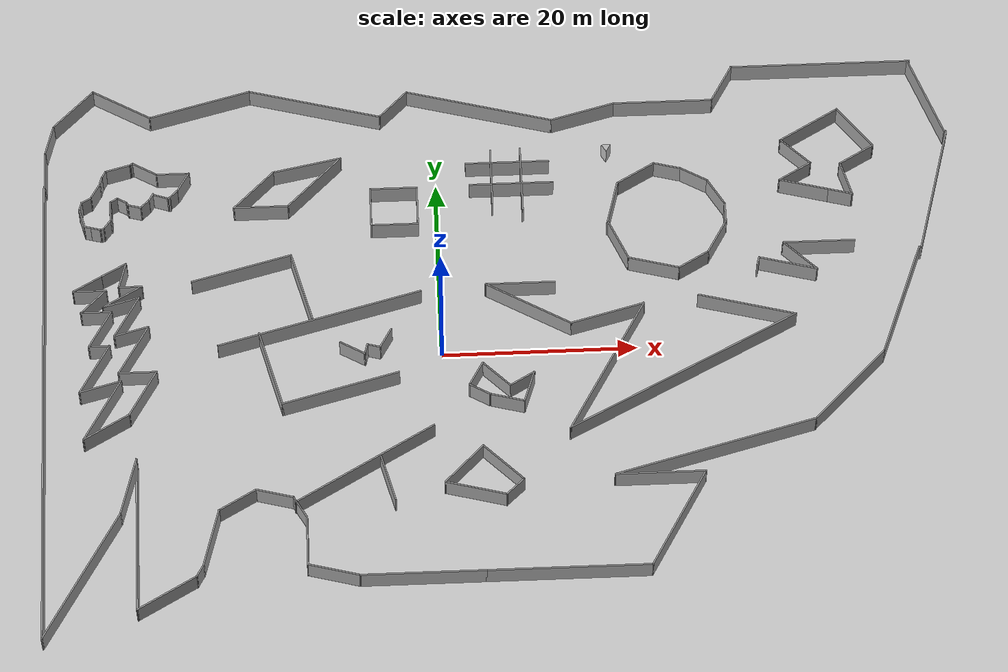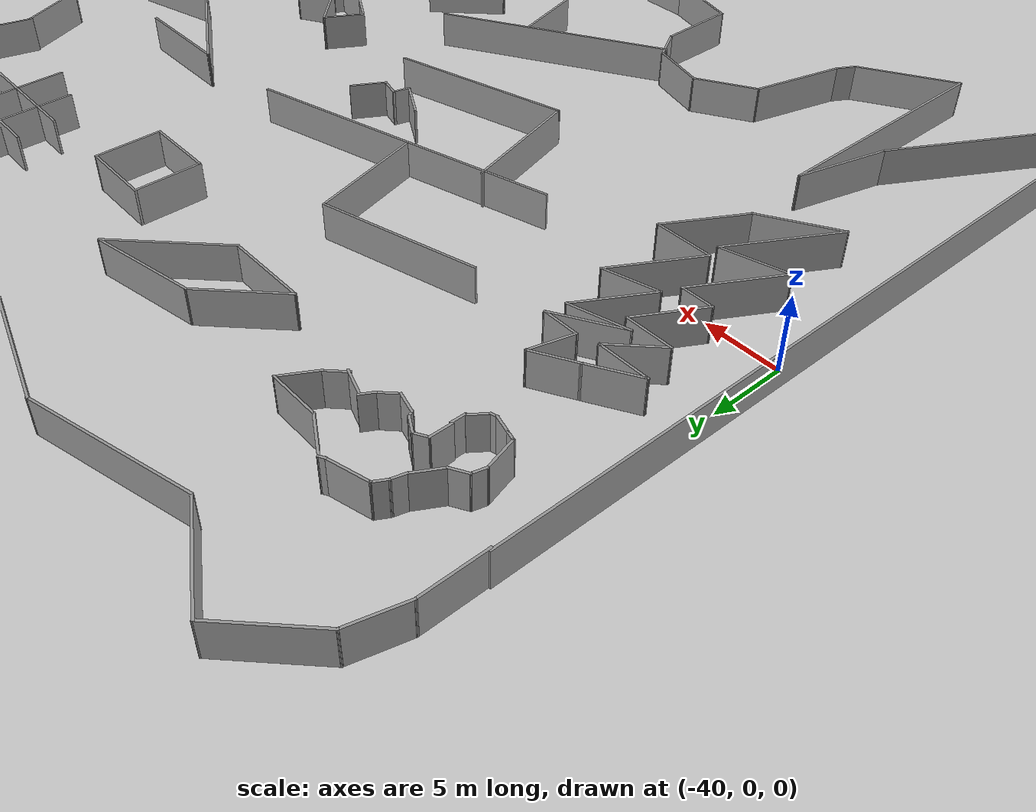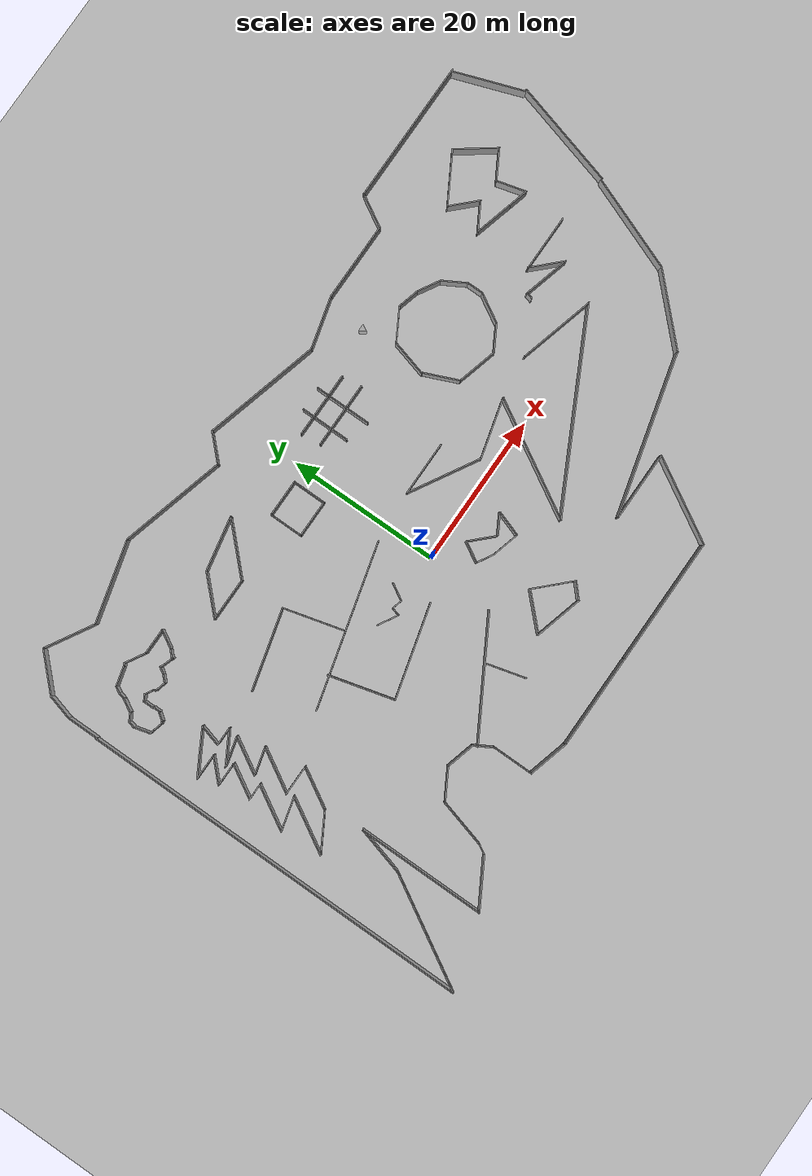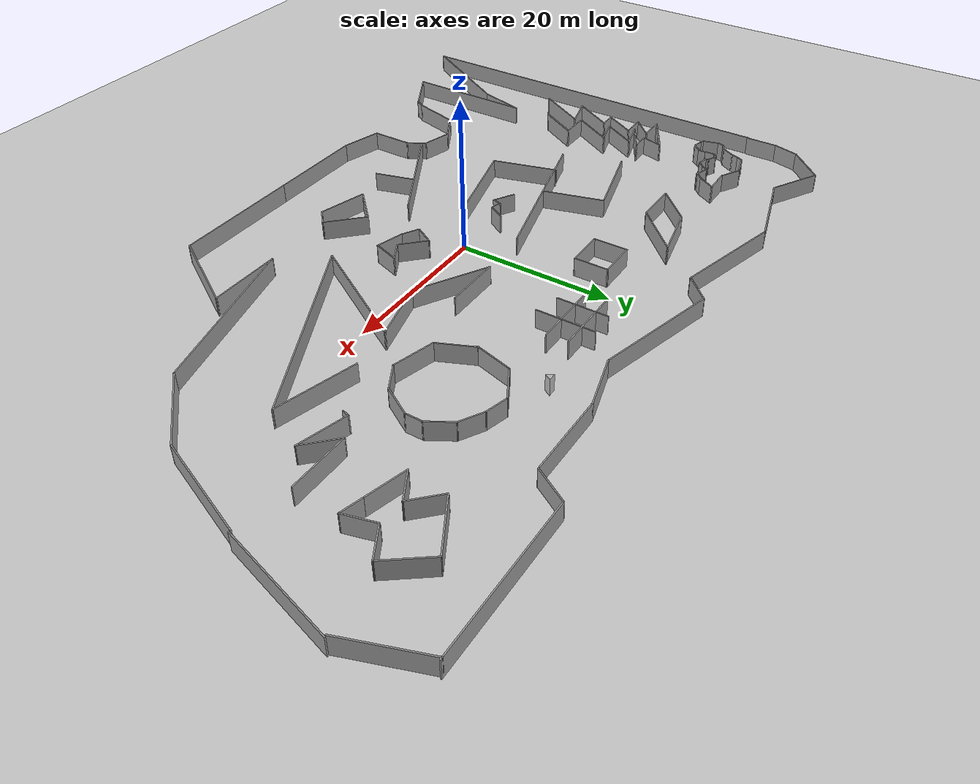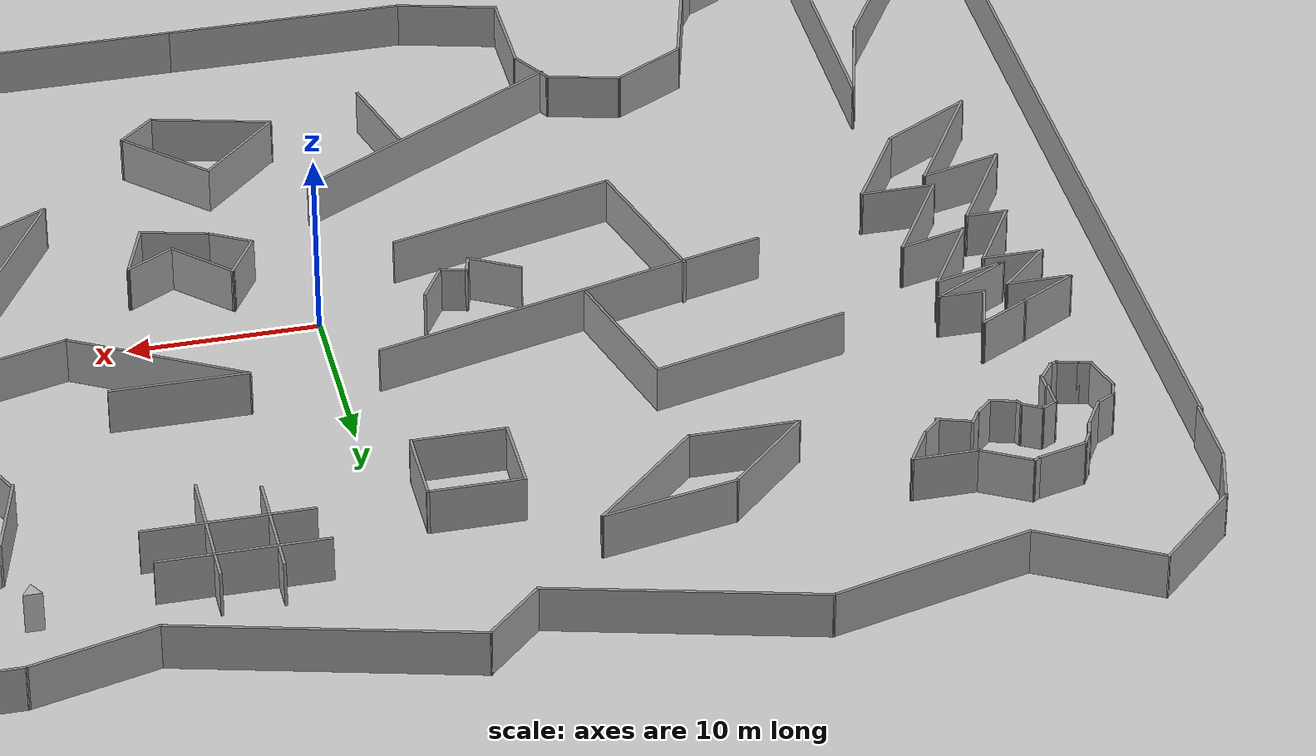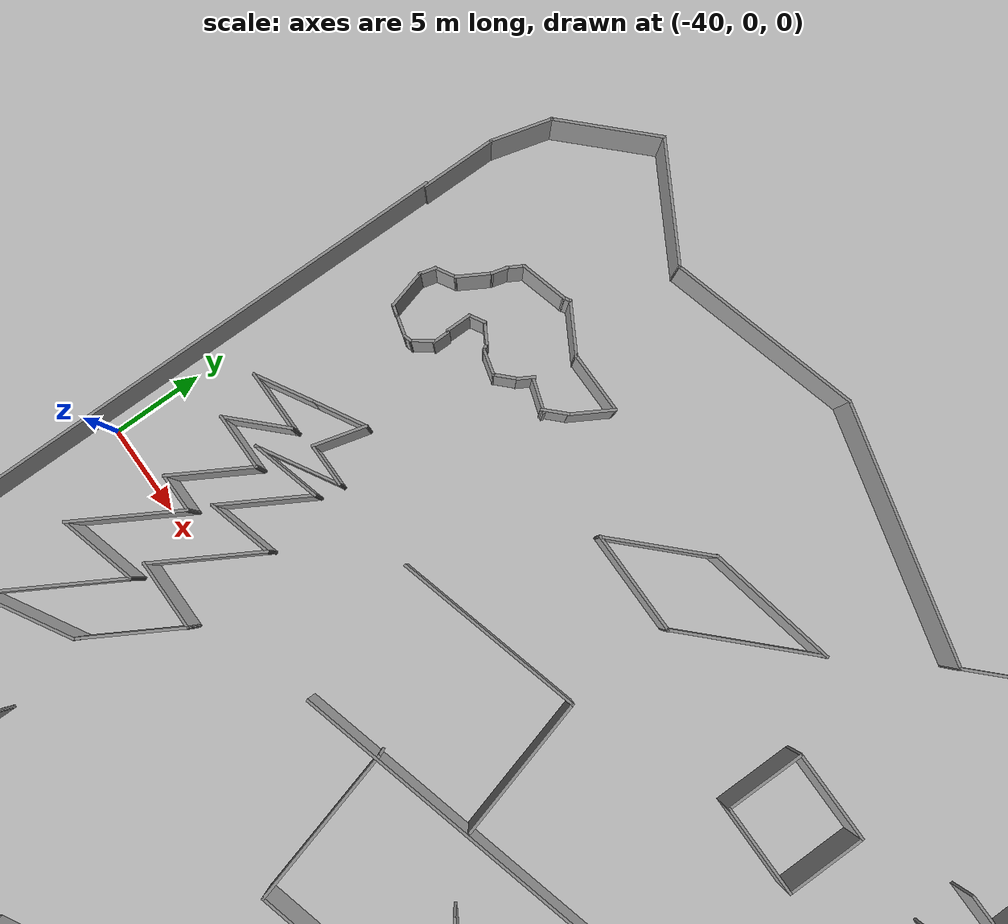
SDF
<sdf version="1.7">
 <world name="default">
  <light name="sun" type="directional">
   <pose>0 0 10 0 -0 0</pose>
   <diffuse>0.8 0.8 0.8 1</diffuse>
   <specular>0.2 0.2 0.2 1</specular>
   <attenuation>
    <range>1000</range>
    <constant>0.9</constant>
    <linear>0.01</linear>
    <quadratic>0.001</quadratic>
   </attenuation>
   <direction>-0.5 0.1 -0.9</direction>
   <spot><inner_angle>0</inner_angle><outer_angle>0</outer_angle><falloff>0</falloff></spot>
  </light>
  <model name="ground_plane">
   <static>1</static>
   <link name="link">
    <collision name="collision">
     <geometry><plane><normal>0 0 1</normal><size>100 100</size></plane></geometry>
     <surface><friction><ode><mu>100</mu><mu2>50</mu2></ode></friction></surface>
    </collision>
    <visual name="visual">
     <cast_shadows>0</cast_shadows>
     <geometry><plane><normal>0 0 1</normal><size>100 100</size></plane></geometry>
     <material>
      <script><uri>file://media/materials/scripts/gazebo.material</uri><name>Gazebo/Grey</name></script>
     </material>
    </visual>
   </link>
  </model>
  <gravity>0 0 -9.8</gravity>
  <magnetic_field>6e-06 2.3e-05 -4.2e-05</magnetic_field>
  <atmosphere type="adiabatic"/>
  <physics type="ode">
   <max_step_size>0.001</max_step_size>
   <real_time_factor>1</real_time_factor>
   <real_time_update_rate>1000</real_time_update_rate>
  </physics>
  <scene><ambient>0.4 0.4 0.4 1</ambient><background>0.7 0.7 0.7 1</background><shadows>1</shadows></scene>
  <audio><device>default</device></audio>
  <spherical_coordinates>
   <surface_model>EARTH_WGS84</surface_model>
   <latitude_deg>0</latitude_deg>
   <longitude_deg>0</longitude_deg>
   <elevation>0</elevation>
   <heading_deg>0</heading_deg>
  </spherical_coordinates>
  <model name="custommap5">
   <pose>6.41757 0.185027 0 0 -0 0</pose>
   <link name="Wall_10">
    <collision name="Wall_10_Collision">
     <geometry><box><size>6.5 0.15 2.5</size></box></geometry>
     <pose>0 0 1.25 0 -0 0</pose>
    </collision>
    <visual name="Wall_10_Visual">
     <pose>0 0 1.25 0 -0 0</pose>
     <geometry><box><size>6.5 0.15 2.5</size></box></geometry>
     <material>
      <script><uri>file://media/materials/scripts/gazebo.material</uri><name>Gazebo/Grey</name></script>
      <ambient>1 1 1 1</ambient>
     </material>
     <meta><layer>0</layer></meta>
    </visual>
    <pose>-30.3175 -21.4493 0 0 -0 1.309</pose>
   </link>
   <link name="Wall_100">
    <collision name="Wall_100_Collision">
     <geometry><box><size>3.25 0.15 2.5</size></box></geometry>
     <pose>0 0 1.25 0 -0 0</pose>
    </collision>
    <visual name="Wall_100_Visual">
     <pose>0 0 1.25 0 -0 0</pose>
     <geometry><box><size>3.25 0.15 2.5</size></box></geometry>
     <material>
      <script><uri>file://media/materials/scripts/gazebo.material</uri><name>Gazebo/Grey</name></script>
      <ambient>1 1 1 1</ambient>
     </material>
     <meta><layer>0</layer></meta>
    </visual>
    <pose>-41.7743 4.90897 0 0 -0 0</pose>
   </link>
   <link name="Wall_101">
    <collision name="Wall_101_Collision">
     <geometry><box><size>4.75 0.15 2.5</size></box></geometry>
     <pose>0 0 1.25 0 -0 0</pose>
    </collision>
    <visual name="Wall_101_Visual">
     <pose>0 0 1.25 0 -0 0</pose>
     <geometry><box><size>4.75 0.15 2.5</size></box></geometry>
     <material>
      <script><uri>file://media/materials/scripts/gazebo.material</uri><name>Gazebo/Grey</name></script>
      <ambient>1 1 1 1</ambient>
     </material>
     <meta><layer>0</layer></meta>
    </visual>
    <pose>-41.3743 2.91711 0 0 -0 -2.0944</pose>
   </link>
   <link name="Wall_102">
    <collision name="Wall_102_Collision">
     <geometry><box><size>2.25 0.15 2.5</size></box></geometry>
     <pose>0 0 1.25 0 -0 0</pose>
    </collision>
    <visual name="Wall_102_Visual">
     <pose>0 0 1.25 0 -0 0</pose>
     <geometry><box><size>2.25 0.15 2.5</size></box></geometry>
     <material>
      <script><uri>file://media/materials/scripts/gazebo.material</uri><name>Gazebo/Grey</name></script>
      <ambient>1 1 1 1</ambient>
     </material>
     <meta><layer>0</layer></meta>
    </visual>
    <pose>-41.4743 0.925256 0 0 -0 0</pose>
   </link>
   <link name="Wall_103">
    <collision name="Wall_103_Collision">
     <geometry><box><size>6.25 0.15 2.5</size></box></geometry>
     <pose>0 0 1.25 0 -0 0</pose>
    </collision>
    <visual name="Wall_103_Visual">
     <pose>0 0 1.25 0 -0 0</pose>
     <geometry><box><size>6.25 0.15 2.5</size></box></geometry>
     <material>
      <script><uri>file://media/materials/scripts/gazebo.material</uri><name>Gazebo/Grey</name></script>
      <ambient>1 1 1 1</ambient>
     </material>
     <meta><layer>0</layer></meta>
    </visual>
    <pose>-41.9493 -1.71612 0 0 -0 -2.0944</pose>
   </link>
   <link name="Wall_104">
    <collision name="Wall_104_Collision">
     <geometry><box><size>4.5 0.15 2.5</size></box></geometry>
     <pose>0 0 1.25 0 -0 0</pose>
    </collision>
    <visual name="Wall_104_Visual">
     <pose>0 0 1.25 0 -0 0</pose>
     <geometry><box><size>4.5 0.15 2.5</size></box></geometry>
     <material>
      <script><uri>file://media/materials/scripts/gazebo.material</uri><name>Gazebo/Grey</name></script>
      <ambient>1 1 1 1</ambient>
     </material>
     <meta><layer>0</layer></meta>
    </visual>
    <pose>-41.3734 -3.79457 0 0 -0 0.261799</pose>
   </link>
   <link name="Wall_105">
    <collision name="Wall_105_Collision">
     <geometry><box><size>7.75 0.15 2.5</size></box></geometry>
     <pose>0 0 1.25 0 -0 0</pose>
    </collision>
    <visual name="Wall_105_Visual">
     <pose>0 0 1.25 0 -0 0</pose>
     <geometry><box><size>7.75 0.15 2.5</size></box></geometry>
     <material>
      <script><uri>file://media/materials/scripts/gazebo.material</uri><name>Gazebo/Grey</name></script>
      <ambient>1 1 1 1</ambient>
     </material>
     <meta><layer>0</layer></meta>
    </visual>
    <pose>-41.1725 -6.52253 0 0 -0 -2.0944</pose>
   </link>
   <link name="Wall_106">
    <collision name="Wall_106_Collision">
     <geometry><box><size>5.5 0.15 2.5</size></box></geometry>
     <pose>0 0 1.25 0 -0 0</pose>
    </collision>
    <visual name="Wall_106_Visual">
     <pose>0 0 1.25 0 -0 0</pose>
     <geometry><box><size>5.5 0.15 2.5</size></box></geometry>
     <material>
      <script><uri>file://media/materials/scripts/gazebo.material</uri><name>Gazebo/Grey</name></script>
      <ambient>1 1 1 1</ambient>
     </material>
     <meta><layer>0</layer></meta>
    </visual>
    <pose>-40.7559 -8.47593 0 0 -0 0.523599</pose>
   </link>
   <link name="Wall_107">
    <collision name="Wall_107_Collision">
     <geometry><box><size>5.75 0.15 2.5</size></box></geometry>
     <pose>0 0 1.25 0 -0 0</pose>
    </collision>
    <visual name="Wall_107_Visual">
     <pose>0 0 1.25 0 -0 0</pose>
     <geometry><box><size>5.75 0.15 2.5</size></box></geometry>
     <material>
      <script><uri>file://media/materials/scripts/gazebo.material</uri><name>Gazebo/Grey</name></script>
      <ambient>1 1 1 1</ambient>
     </material>
     <meta><layer>0</layer></meta>
    </visual>
    <pose>-37.0393 -4.71356 0 0 -0 1.0472</pose>
   </link>
   <link name="Wall_108">
    <collision name="Wall_108_Collision">
     <geometry><box><size>4 0.15 2.5</size></box></geometry>
     <pose>0 0 1.25 0 -0 0</pose>
    </collision>
    <visual name="Wall_108_Visual">
     <pose>0 0 1.25 0 -0 0</pose>
     <geometry><box><size>4 0.15 2.5</size></box></geometry>
     <material>
      <script><uri>file://media/materials/scripts/gazebo.material</uri><name>Gazebo/Grey</name></script>
      <ambient>1 1 1 1</ambient>
     </material>
     <meta><layer>0</layer></meta>
    </visual>
    <pose>-37.5643 -2.28869 0 0 -0 3.14159</pose>
   </link>
   <link name="Wall_109">
    <collision name="Wall_109_Collision">
     <geometry><box><size>6.25 0.15 2.5</size></box></geometry>
     <pose>0 0 1.25 0 -0 0</pose>
    </collision>
    <visual name="Wall_109_Visual">
     <pose>0 0 1.25 0 -0 0</pose>
     <geometry><box><size>6.25 0.15 2.5</size></box></geometry>
     <material>
      <script><uri>file://media/materials/scripts/gazebo.material</uri><name>Gazebo/Grey</name></script>
      <ambient>1 1 1 1</ambient>
     </material>
     <meta><layer>0</layer></meta>
    </visual>
    <pose>-37.9643 0.352691 0 0 -0 1.0472</pose>
   </link>
   <link name="Wall_11">
    <collision name="Wall_11_Collision">
     <geometry><box><size>4.5 0.15 2.5</size></box></geometry>
     <pose>0 0 1.25 0 -0 0</pose>
    </collision>
    <visual name="Wall_11_Visual">
     <pose>0 0 1.25 0 -0 0</pose>
     <geometry><box><size>4.5 0.15 2.5</size></box></geometry>
     <material>
      <script><uri>file://media/materials/scripts/gazebo.material</uri><name>Gazebo/Grey</name></script>
      <ambient>1 1 1 1</ambient>
     </material>
     <meta><layer>0</layer></meta>
    </visual>
    <pose>-27.6121 -17.295 0 0 -0 0.523599</pose>
   </link>
   <link name="Wall_110">
    <collision name="Wall_110_Collision">
     <geometry><box><size>3.75 0.15 2.5</size></box></geometry>
     <pose>0 0 1.25 0 -0 0</pose>
    </collision>
    <visual name="Wall_110_Visual">
     <pose>0 0 1.25 0 -0 0</pose>
     <geometry><box><size>3.75 0.15 2.5</size></box></geometry>
     <material>
      <script><uri>file://media/materials/scripts/gazebo.material</uri><name>Gazebo/Grey</name></script>
      <ambient>1 1 1 1</ambient>
     </material>
     <meta><layer>0</layer></meta>
    </visual>
    <pose>-38.1779 2.52819 0 0 -0 -2.87979</pose>
   </link>
   <link name="Wall_111">
    <collision name="Wall_111_Collision">
     <geometry><box><size>5.25 0.15 2.5</size></box></geometry>
     <pose>0 0 1.25 0 -0 0</pose>
    </collision>
    <visual name="Wall_111_Visual">
     <pose>0 0 1.25 0 -0 0</pose>
     <geometry><box><size>5.25 0.15 2.5</size></box></geometry>
     <material>
      <script><uri>file://media/materials/scripts/gazebo.material</uri><name>Gazebo/Grey</name></script>
      <ambient>1 1 1 1</ambient>
     </material>
     <meta><layer>0</layer></meta>
    </visual>
    <pose>-38.6416 4.27068 0 0 -0 1.0472</pose>
   </link>
   <link name="Wall_112">
    <collision name="Wall_112_Collision">
     <geometry><box><size>4 0.15 2.5</size></box></geometry>
     <pose>0 0 1.25 0 -0 0</pose>
    </collision>
    <visual name="Wall_112_Visual">
     <pose>0 0 1.25 0 -0 0</pose>
     <geometry><box><size>4 0.15 2.5</size></box></geometry>
     <material>
      <script><uri>file://media/materials/scripts/gazebo.material</uri><name>Gazebo/Grey</name></script>
      <ambient>1 1 1 1</ambient>
     </material>
     <meta><layer>0</layer></meta>
    </visual>
    <pose>-39.226 5.98082 0 0 -0 -2.87979</pose>
   </link>
   <link name="Wall_113">
    <collision name="Wall_113_Collision">
     <geometry><box><size>4.75 0.15 2.5</size></box></geometry>
     <pose>0 0 1.25 0 -0 0</pose>
    </collision>
    <visual name="Wall_113_Visual">
     <pose>0 0 1.25 0 -0 0</pose>
     <geometry><box><size>4.75 0.15 2.5</size></box></geometry>
     <material>
      <script><uri>file://media/materials/scripts/gazebo.material</uri><name>Gazebo/Grey</name></script>
      <ambient>1 1 1 1</ambient>
     </material>
     <meta><layer>0</layer></meta>
    </visual>
    <pose>-39.0936 6.6326 0 0 -0 0.523599</pose>
   </link>
   <link name="Wall_114">
    <collision name="Wall_114_Collision">
     <geometry><box><size>2.5 0.15 2.5</size></box></geometry>
     <pose>0 0 1.25 0 -0 0</pose>
    </collision>
    <visual name="Wall_114_Visual">
     <pose>0 0 1.25 0 -0 0</pose>
     <geometry><box><size>2.5 0.15 2.5</size></box></geometry>
     <material>
      <script><uri>file://media/materials/scripts/gazebo.material</uri><name>Gazebo/Grey</name></script>
      <ambient>1 1 1 1</ambient>
     </material>
     <meta><layer>0</layer></meta>
    </visual>
    <pose>-38.2767 7.7826 0 0 -0 3.14159</pose>
   </link>
   <link name="Wall_115">
    <collision name="Wall_115_Collision">
     <geometry><box><size>3 0.15 2.5</size></box></geometry>
     <pose>0 0 1.25 0 -0 0</pose>
    </collision>
    <visual name="Wall_115_Visual">
     <pose>0 0 1.25 0 -0 0</pose>
     <geometry><box><size>3 0.15 2.5</size></box></geometry>
     <material>
      <script><uri>file://media/materials/scripts/gazebo.material</uri><name>Gazebo/Grey</name></script>
      <ambient>1 1 1 1</ambient>
     </material>
     <meta><layer>0</layer></meta>
    </visual>
    <pose>-39.0829 9.15904 0 0 -0 1.309</pose>
   </link>
   <link name="Wall_116">
    <collision name="Wall_116_Collision">
     <geometry><box><size>3.02994 0.15 2.5</size></box></geometry>
     <pose>0 0 1.25 0 -0 0</pose>
    </collision>
    <visual name="Wall_116_Visual">
     <pose>0 0 1.25 0 -0 0</pose>
     <geometry><box><size>3.02994 0.15 2.5</size></box></geometry>
     <material>
      <script><uri>file://media/materials/scripts/gazebo.material</uri><name>Gazebo/Grey</name></script>
      <ambient>1 1 1 1</ambient>
     </material>
     <meta><layer>0</layer></meta>
    </visual>
    <pose>-39.9708 9.83252 0 0 -0 -2.63159</pose>
   </link>
   <link name="Wall_118">
    <collision name="Wall_118_Collision">
     <geometry><box><size>3 0.15 2.5</size></box></geometry>
     <pose>0 0 1.25 0 -0 0</pose>
    </collision>
    <visual name="Wall_118_Visual">
     <pose>0 0 1.25 0 -0 0</pose>
     <geometry><box><size>3 0.15 2.5</size></box></geometry>
     <material>
      <script><uri>file://media/materials/scripts/gazebo.material</uri><name>Gazebo/Grey</name></script>
      <ambient>1 1 1 1</ambient>
     </material>
     <meta><layer>0</layer></meta>
    </visual>
    <pose>1.5599 -4.60224 0 0 -0 -2.61799</pose>
   </link>
   <link name="Wall_119">
    <collision name="Wall_119_Collision">
     <geometry><box><size>4 0.15 2.5</size></box></geometry>
     <pose>0 0 1.25 0 -0 0</pose>
    </collision>
    <visual name="Wall_119_Visual">
     <pose>0 0 1.25 0 -0 0</pose>
     <geometry><box><size>4 0.15 2.5</size></box></geometry>
     <material>
      <script><uri>file://media/materials/scripts/gazebo.material</uri><name>Gazebo/Grey</name></script>
      <ambient>1 1 1 1</ambient>
     </material>
     <meta><layer>0</layer></meta>
    </visual>
    <pose>-1.03537 -3.95356 0 0 -0 2.35619</pose>
   </link>
   <link name="Wall_12">
    <collision name="Wall_12_Collision">
     <geometry><box><size>4 0.15 2.5</size></box></geometry>
     <pose>0 0 1.25 0 -0 0</pose>
    </collision>
    <visual name="Wall_12_Visual">
     <pose>0 0 1.25 0 -0 0</pose>
     <geometry><box><size>4 0.15 2.5</size></box></geometry>
     <material>
      <script><uri>file://media/materials/scripts/gazebo.material</uri><name>Gazebo/Grey</name></script>
      <ambient>1 1 1 1</ambient>
     </material>
     <meta><layer>0</layer></meta>
    </visual>
    <pose>-23.8691 -16.7057 0 0 -0 -0.261799</pose>
   </link>
   <link name="Wall_120">
    <collision name="Wall_120_Collision">
     <geometry><box><size>3 0.15 2.5</size></box></geometry>
     <pose>0 0 1.25 0 -0 0</pose>
    </collision>
    <visual name="Wall_120_Visual">
     <pose>0 0 1.25 0 -0 0</pose>
     <geometry><box><size>3 0.15 2.5</size></box></geometry>
     <material>
      <script><uri>file://media/materials/scripts/gazebo.material</uri><name>Gazebo/Grey</name></script>
      <ambient>1 1 1 1</ambient>
     </material>
     <meta><layer>0</layer></meta>
    </visual>
    <pose>-3.10905 -3.82647 0 0 -0 -2.0944</pose>
   </link>
   <link name="Wall_121">
    <collision name="Wall_121_Collision">
     <geometry><box><size>2.5 0.15 2.5</size></box></geometry>
     <pose>0 0 1.25 0 -0 0</pose>
    </collision>
    <visual name="Wall_121_Visual">
     <pose>0 0 1.25 0 -0 0</pose>
     <geometry><box><size>2.5 0.15 2.5</size></box></geometry>
     <material>
      <script><uri>file://media/materials/scripts/gazebo.material</uri><name>Gazebo/Grey</name></script>
      <ambient>1 1 1 1</ambient>
     </material>
     <meta><layer>0</layer></meta>
    </visual>
    <pose>-2.80397 -5.64805 0 0 -0 -0.523599</pose>
   </link>
   <link name="Wall_122">
    <collision name="Wall_122_Collision">
     <geometry><box><size>3.75 0.15 2.5</size></box></geometry>
     <pose>0 0 1.25 0 -0 0</pose>
    </collision>
    <visual name="Wall_122_Visual">
     <pose>0 0 1.25 0 -0 0</pose>
     <geometry><box><size>3.75 0.15 2.5</size></box></geometry>
     <material>
      <script><uri>file://media/materials/scripts/gazebo.material</uri><name>Gazebo/Grey</name></script>
      <ambient>1 1 1 1</ambient>
     </material>
     <meta><layer>0</layer></meta>
    </visual>
    <pose>-0.047719 -6.70143 0 0 -0 -0.261799</pose>
   </link>
   <link name="Wall_123">
    <collision name="Wall_123_Collision">
     <geometry><box><size>3.60819 0.15 2.5</size></box></geometry>
     <pose>0 0 1.25 0 -0 0</pose>
    </collision>
    <visual name="Wall_123_Visual">
     <pose>0 0 1.25 0 -0 0</pose>
     <geometry><box><size>3.60819 0.15 2.5</size></box></geometry>
     <material>
      <script><uri>file://media/materials/scripts/gazebo.material</uri><name>Gazebo/Grey</name></script>
      <ambient>1 1 1 1</ambient>
     </material>
     <meta><layer>0</layer></meta>
    </visual>
    <pose>2.24247 -5.52852 0 0 -0 1.24616</pose>
   </link>
   <link name="Wall_125">
    <collision name="Wall_125_Collision">
     <geometry><box><size>7.25 0.15 2.5</size></box></geometry>
     <pose>0 0 1.25 0 -0 0</pose>
    </collision>
    <visual name="Wall_125_Visual">
     <pose>0 0 1.25 0 -0 0</pose>
     <geometry><box><size>7.25 0.15 2.5</size></box></geometry>
     <material>
      <script><uri>file://media/materials/scripts/gazebo.material</uri><name>Gazebo/Grey</name></script>
      <ambient>1 1 1 1</ambient>
     </material>
     <meta><layer>0</layer></meta>
    </visual>
    <pose>1.84785 6.60707 0 0 -0 3.14159</pose>
   </link>
   <link name="Wall_126">
    <collision name="Wall_126_Collision">
     <geometry><box><size>10 0.15 2.5</size></box></geometry>
     <pose>0 0 1.25 0 -0 0</pose>
    </collision>
    <visual name="Wall_126_Visual">
     <pose>0 0 1.25 0 -0 0</pose>
     <geometry><box><size>10 0.15 2.5</size></box></geometry>
     <material>
      <script><uri>file://media/materials/scripts/gazebo.material</uri><name>Gazebo/Grey</name></script>
      <ambient>1 1 1 1</ambient>
     </material>
     <meta><layer>0</layer></meta>
    </visual>
    <pose>2.56302 4.14457 0 0 -0 -0.523599</pose>
   </link>
   <link name="Wall_127">
    <collision name="Wall_127_Collision">
     <geometry><box><size>8 0.15 2.5</size></box></geometry>
     <pose>0 0 1.25 0 -0 0</pose>
    </collision>
    <visual name="Wall_127_Visual">
     <pose>0 0 1.25 0 -0 0</pose>
     <geometry><box><size>8 0.15 2.5</size></box></geometry>
     <material>
      <script><uri>file://media/materials/scripts/gazebo.material</uri><name>Gazebo/Grey</name></script>
      <ambient>1 1 1 1</ambient>
     </material>
     <meta><layer>0</layer></meta>
    </visual>
    <pose>10.6195 2.69793 0 0 -0 0.261799</pose>
   </link>
   <link name="Wall_128">
    <collision name="Wall_128_Collision">
     <geometry><box><size>16.5 0.15 2.5</size></box></geometry>
     <pose>0 0 1.25 0 -0 0</pose>
    </collision>
    <visual name="Wall_128_Visual">
     <pose>0 0 1.25 0 -0 0</pose>
     <geometry><box><size>16.5 0.15 2.5</size></box></geometry>
     <material>
      <script><uri>file://media/materials/scripts/gazebo.material</uri><name>Gazebo/Grey</name></script>
      <ambient>1 1 1 1</ambient>
     </material>
     <meta><layer>0</layer></meta>
    </visual>
    <pose>10.3232 -3.36596 0 0 -0 -2.0944</pose>
   </link>
   <link name="Wall_129">
    <collision name="Wall_129_Collision">
     <geometry><box><size>26.8353 0.15 2.5</size></box></geometry>
     <pose>0 0 1.25 0 -0 0</pose>
    </collision>
    <visual name="Wall_129_Visual">
     <pose>0 0 1.25 0 -0 0</pose>
     <geometry><box><size>26.8353 0.15 2.5</size></box></geometry>
     <material>
      <script><uri>file://media/materials/scripts/gazebo.material</uri><name>Gazebo/Grey</name></script>
      <ambient>1 1 1 1</ambient>
     </material>
     <meta><layer>0</layer></meta>
    </visual>
    <pose>18.0786 -4.29987 0 0 -0 0.478691</pose>
   </link>
   <link name="Wall_13">
    <collision name="Wall_13_Collision">
     <geometry><box><size>2.75 0.15 2.5</size></box></geometry>
     <pose>0 0 1.25 0 -0 0</pose>
    </collision>
    <visual name="Wall_13_Visual">
     <pose>0 0 1.25 0 -0 0</pose>
     <geometry><box><size>2.75 0.15 2.5</size></box></geometry>
     <material>
      <script><uri>file://media/materials/scripts/gazebo.material</uri><name>Gazebo/Grey</name></script>
      <ambient>1 1 1 1</ambient>
     </material>
     <meta><layer>0</layer></meta>
    </visual>
    <pose>-21.3597 -18.3297 0 0 -0 -1.0472</pose>
   </link>
   <link name="Wall_130">
    <collision name="Wall_130_Collision">
     <geometry><box><size>10.25 0.15 2.5</size></box></geometry>
     <pose>0 0 1.25 0 -0 0</pose>
    </collision>
    <visual name="Wall_130_Visual">
     <pose>0 0 1.25 0 -0 0</pose>
     <geometry><box><size>10.25 0.15 2.5</size></box></geometry>
     <material>
      <script><uri>file://media/materials/scripts/gazebo.material</uri><name>Gazebo/Grey</name></script>
      <ambient>1 1 1 1</ambient>
     </material>
     <meta><layer>0</layer></meta>
    </visual>
    <pose>24.9622 3.15302 0 0 -0 2.87979</pose>
   </link>
   <link name="Wall_132">
    <collision name="Wall_132_Collision">
     <geometry><box><size>16.5 0.15 2.5</size></box></geometry>
     <pose>0 0 1.25 0 -0 0</pose>
    </collision>
    <visual name="Wall_132_Visual">
     <pose>0 0 1.25 0 -0 0</pose>
     <geometry><box><size>16.5 0.15 2.5</size></box></geometry>
     <material>
      <script><uri>file://media/materials/scripts/gazebo.material</uri><name>Gazebo/Grey</name></script>
      <ambient>1 1 1 1</ambient>
     </material>
     <meta><layer>0</layer></meta>
    </visual>
    <pose>-14.7012 -13.6732 0 0 -0 -2.61799</pose>
   </link>
   <link name="Wall_134">
    <collision name="Wall_134_Collision">
     <geometry><box><size>5.25 0.15 2.5</size></box></geometry>
     <pose>0 0 1.25 0 -0 0</pose>
    </collision>
    <visual name="Wall_134_Visual">
     <pose>0 0 1.25 0 -0 0</pose>
     <geometry><box><size>5.25 0.15 2.5</size></box></geometry>
     <material>
      <script><uri>file://media/materials/scripts/gazebo.material</uri><name>Gazebo/Grey</name></script>
      <ambient>1 1 1 1</ambient>
     </material>
     <meta><layer>0</layer></meta>
    </visual>
    <pose>-12.4133 -15.385 0 0 -0 -1.309</pose>
   </link>
   <link name="Wall_136">
    <collision name="Wall_136_Collision">
     <geometry><box><size>5.75 0.15 2.5</size></box></geometry>
     <pose>0 0 1.25 0 -0 0</pose>
    </collision>
    <visual name="Wall_136_Visual">
     <pose>0 0 1.25 0 -0 0</pose>
     <geometry><box><size>5.75 0.15 2.5</size></box></geometry>
     <material>
      <script><uri>file://media/materials/scripts/gazebo.material</uri><name>Gazebo/Grey</name></script>
      <ambient>1 1 1 1</ambient>
     </material>
     <meta><layer>0</layer></meta>
    </visual>
    <pose>-0.731953 -14.1154 0 0 -0 2.35619</pose>
   </link>
   <link name="Wall_137">
    <collision name="Wall_137_Collision">
     <geometry><box><size>5.75 0.15 2.5</size></box></geometry>
     <pose>0 0 1.25 0 -0 0</pose>
    </collision>
    <visual name="Wall_137_Visual">
     <pose>0 0 1.25 0 -0 0</pose>
     <geometry><box><size>5.75 0.15 2.5</size></box></geometry>
     <material>
      <script><uri>file://media/materials/scripts/gazebo.material</uri><name>Gazebo/Grey</name></script>
      <ambient>1 1 1 1</ambient>
     </material>
     <meta><layer>0</layer></meta>
    </visual>
    <pose>-4.69175 -14.1154 0 0 -0 -2.35619</pose>
   </link>
   <link name="Wall_138">
    <collision name="Wall_138_Collision">
     <geometry><box><size>6.5 0.15 2.5</size></box></geometry>
     <pose>0 0 1.25 0 -0 0</pose>
    </collision>
    <visual name="Wall_138_Visual">
     <pose>0 0 1.25 0 -0 0</pose>
     <geometry><box><size>6.5 0.15 2.5</size></box></geometry>
     <material>
      <script><uri>file://media/materials/scripts/gazebo.material</uri><name>Gazebo/Grey</name></script>
      <ambient>1 1 1 1</ambient>
     </material>
     <meta><layer>0</layer></meta>
    </visual>
    <pose>-3.60484 -16.9171 0 0 -0 -0.261799</pose>
   </link>
   <link name="Wall_139">
    <collision name="Wall_139_Collision">
     <geometry><box><size>2.57709 0.15 2.5</size></box></geometry>
     <pose>0 0 1.25 0 -0 0</pose>
    </collision>
    <visual name="Wall_139_Visual">
     <pose>0 0 1.25 0 -0 0</pose>
     <geometry><box><size>2.57709 0.15 2.5</size></box></geometry>
     <material>
      <script><uri>file://media/materials/scripts/gazebo.material</uri><name>Gazebo/Grey</name></script>
      <ambient>1 1 1 1</ambient>
     </material>
     <meta><layer>0</layer></meta>
    </visual>
    <pose>0.354963 -16.9171 0 0 -0 0.74388</pose>
   </link>
   <link name="Wall_14">
    <collision name="Wall_14_Collision">
     <geometry><box><size>5.5 0.15 2.5</size></box></geometry>
     <pose>0 0 1.25 0 -0 0</pose>
    </collision>
    <visual name="Wall_14_Visual">
     <pose>0 0 1.25 0 -0 0</pose>
     <geometry><box><size>5.5 0.15 2.5</size></box></geometry>
     <material>
      <script><uri>file://media/materials/scripts/gazebo.material</uri><name>Gazebo/Grey</name></script>
      <ambient>1 1 1 1</ambient>
     </material>
     <meta><layer>0</layer></meta>
    </visual>
    <pose>-20.7097 -22.1306 0 0 -0 -1.5708</pose>
   </link>
   <link name="Wall_141">
    <collision name="Wall_141_Collision">
     <geometry><box><size>6 0.15 2.5</size></box></geometry>
     <pose>0 0 1.25 0 -0 0</pose>
    </collision>
    <visual name="Wall_141_Visual">
     <pose>0 0 1.25 0 -0 0</pose>
     <geometry><box><size>6 0.15 2.5</size></box></geometry>
     <material>
      <script><uri>file://media/materials/scripts/gazebo.material</uri><name>Gazebo/Grey</name></script>
      <ambient>1 1 1 1</ambient>
     </material>
     <meta><layer>0</layer></meta>
    </visual>
    <pose>-25.3943 18.86 0 0 -0 -2.35619</pose>
   </link>
   <link name="Wall_142">
    <collision name="Wall_142_Collision">
     <geometry><box><size>5.75 0.15 2.5</size></box></geometry>
     <pose>0 0 1.25 0 -0 0</pose>
    </collision>
    <visual name="Wall_142_Visual">
     <pose>0 0 1.25 0 -0 0</pose>
     <geometry><box><size>5.75 0.15 2.5</size></box></geometry>
     <material>
      <script><uri>file://media/materials/scripts/gazebo.material</uri><name>Gazebo/Grey</name></script>
      <ambient>1 1 1 1</ambient>
     </material>
     <meta><layer>0</layer></meta>
    </visual>
    <pose>-24.6626 16.7917 0 0 -0 0</pose>
   </link>
   <link name="Wall_143">
    <collision name="Wall_143_Collision">
     <geometry><box><size>8 0.15 2.5</size></box></geometry>
     <pose>0 0 1.25 0 -0 0</pose>
    </collision>
    <visual name="Wall_143_Visual">
     <pose>0 0 1.25 0 -0 0</pose>
     <geometry><box><size>8 0.15 2.5</size></box></geometry>
     <material>
      <script><uri>file://media/materials/scripts/gazebo.material</uri><name>Gazebo/Grey</name></script>
      <ambient>1 1 1 1</ambient>
     </material>
     <meta><layer>0</layer></meta>
    </visual>
    <pose>-19.0872 19.5671 0 0 -0 0.785398</pose>
   </link>
   <link name="Wall_144">
    <collision name="Wall_144_Collision">
     <geometry><box><size>7.30536 0.15 2.5</size></box></geometry>
     <pose>0 0 1.25 0 -0 0</pose>
    </collision>
    <visual name="Wall_144_Visual">
     <pose>0 0 1.25 0 -0 0</pose>
     <geometry><box><size>7.30536 0.15 2.5</size></box></geometry>
     <material>
      <script><uri>file://media/materials/scripts/gazebo.material</uri><name>Gazebo/Grey</name></script>
      <ambient>1 1 1 1</ambient>
     </material>
     <meta><layer>0</layer></meta>
    </visual>
    <pose>-19.8189 21.6354 0 0 -0 -2.94264</pose>
   </link>
   <link name="Wall_146">
    <collision name="Wall_146_Collision">
     <geometry><box><size>6.5 0.15 2.5</size></box></geometry>
     <pose>0 0 1.25 0 -0 0</pose>
    </collision>
    <visual name="Wall_146_Visual">
     <pose>0 0 1.25 0 -0 0</pose>
     <geometry><box><size>6.5 0.15 2.5</size></box></geometry>
     <material>
      <script><uri>file://media/materials/scripts/gazebo.material</uri><name>Gazebo/Grey</name></script>
      <ambient>1 1 1 1</ambient>
     </material>
     <meta><layer>0</layer></meta>
    </visual>
    <pose>-0.631779 19.4863 0 0 -0 -1.5708</pose>
   </link>
   <link name="Wall_148">
    <collision name="Wall_148_Collision">
     <geometry><box><size>7.5 0.15 2.5</size></box></geometry>
     <pose>0 0 1.25 0 -0 0</pose>
    </collision>
    <visual name="Wall_148_Visual">
     <pose>0 0 1.25 0 -0 0</pose>
     <geometry><box><size>7.5 0.15 2.5</size></box></geometry>
     <material>
      <script><uri>file://media/materials/scripts/gazebo.material</uri><name>Gazebo/Grey</name></script>
      <ambient>1 1 1 1</ambient>
     </material>
     <meta><layer>0</layer></meta>
    </visual>
    <pose>2.48899 19.0939 0 0 -0 -1.5708</pose>
   </link>
   <link name="Wall_15">
    <collision name="Wall_15_Collision">
     <geometry><box><size>5.5 0.15 2.5</size></box></geometry>
     <pose>0 0 1.25 0 -0 0</pose>
    </collision>
    <visual name="Wall_15_Visual">
     <pose>0 0 1.25 0 -0 0</pose>
     <geometry><box><size>5.5 0.15 2.5</size></box></geometry>
     <material>
      <script><uri>file://media/materials/scripts/gazebo.material</uri><name>Gazebo/Grey</name></script>
      <ambient>1 1 1 1</ambient>
     </material>
     <meta><layer>0</layer></meta>
    </visual>
    <pose>-18.1258 -25.4979 0 0 -0 -0.261799</pose>
   </link>
   <link name="Wall_150">
    <collision name="Wall_150_Collision">
     <geometry><box><size>8.75 0.15 2.5</size></box></geometry>
     <pose>0 0 1.25 0 -0 0</pose>
    </collision>
    <visual name="Wall_150_Visual">
     <pose>0 0 1.25 0 -0 0</pose>
     <geometry><box><size>8.75 0.15 2.5</size></box></geometry>
     <material>
      <script><uri>file://media/materials/scripts/gazebo.material</uri><name>Gazebo/Grey</name></script>
      <ambient>1 1 1 1</ambient>
     </material>
     <meta><layer>0</layer></meta>
    </visual>
    <pose>1.08552 21.1547 0 0 -0 0</pose>
   </link>
   <link name="Wall_152">
    <collision name="Wall_152_Collision">
     <geometry><box><size>8.75 0.15 2.5</size></box></geometry>
     <pose>0 0 1.25 0 -0 0</pose>
    </collision>
    <visual name="Wall_152_Visual">
     <pose>0 0 1.25 0 -0 0</pose>
     <geometry><box><size>8.75 0.15 2.5</size></box></geometry>
     <material>
      <script><uri>file://media/materials/scripts/gazebo.material</uri><name>Gazebo/Grey</name></script>
      <ambient>1 1 1 1</ambient>
     </material>
     <meta><layer>0</layer></meta>
    </visual>
    <pose>1.40836 18.572 0 0 -0 0</pose>
   </link>
   <link name="Wall_154">
    <collision name="Wall_154_Collision">
     <geometry><box><size>7.25 0.15 2.5</size></box></geometry>
     <pose>0 0 1.25 0 -0 0</pose>
    </collision>
    <visual name="Wall_154_Visual">
     <pose>0 0 1.25 0 -0 0</pose>
     <geometry><box><size>7.25 0.15 2.5</size></box></geometry>
     <material>
      <script><uri>file://media/materials/scripts/gazebo.material</uri><name>Gazebo/Grey</name></script>
      <ambient>1 1 1 1</ambient>
     </material>
     <meta><layer>0</layer></meta>
    </visual>
    <pose>32.8624 24.4607 0 0 -0 -2.61799</pose>
   </link>
   <link name="Wall_155">
    <collision name="Wall_155_Collision">
     <geometry><box><size>4.25 0.15 2.5</size></box></geometry>
     <pose>0 0 1.25 0 -0 0</pose>
    </collision>
    <visual name="Wall_155_Visual">
     <pose>0 0 1.25 0 -0 0</pose>
     <geometry><box><size>4.25 0.15 2.5</size></box></geometry>
     <material>
      <script><uri>file://media/materials/scripts/gazebo.material</uri><name>Gazebo/Grey</name></script>
      <ambient>1 1 1 1</ambient>
     </material>
     <meta><layer>0</layer></meta>
    </visual>
    <pose>31.2375 21.2362 0 0 -0 -0.785398</pose>
   </link>
   <link name="Wall_156">
    <collision name="Wall_156_Collision">
     <geometry><box><size>4 0.15 2.5</size></box></geometry>
     <pose>0 0 1.25 0 -0 0</pose>
    </collision>
    <visual name="Wall_156_Visual">
     <pose>0 0 1.25 0 -0 0</pose>
     <geometry><box><size>4 0.15 2.5</size></box></geometry>
     <material>
      <script><uri>file://media/materials/scripts/gazebo.material</uri><name>Gazebo/Grey</name></script>
      <ambient>1 1 1 1</ambient>
     </material>
     <meta><layer>0</layer></meta>
    </visual>
    <pose>31.02 18.8241 0 0 -0 -2.61799</pose>
   </link>
   <link name="Wall_157">
    <collision name="Wall_157_Collision">
     <geometry><box><size>5.25 0.15 2.5</size></box></geometry>
     <pose>0 0 1.25 0 -0 0</pose>
    </collision>
    <visual name="Wall_157_Visual">
     <pose>0 0 1.25 0 -0 0</pose>
     <geometry><box><size>5.25 0.15 2.5</size></box></geometry>
     <material>
      <script><uri>file://media/materials/scripts/gazebo.material</uri><name>Gazebo/Grey</name></script>
      <ambient>1 1 1 1</ambient>
     </material>
     <meta><layer>0</layer></meta>
    </visual>
    <pose>31.816 17.2016 0 0 -0 -0.261799</pose>
   </link>
   <link name="Wall_158">
    <collision name="Wall_158_Collision">
     <geometry><box><size>2.75 0.15 2.5</size></box></geometry>
     <pose>0 0 1.25 0 -0 0</pose>
    </collision>
    <visual name="Wall_158_Visual">
     <pose>0 0 1.25 0 -0 0</pose>
     <geometry><box><size>2.75 0.15 2.5</size></box></geometry>
     <material>
      <script><uri>file://media/materials/scripts/gazebo.material</uri><name>Gazebo/Grey</name></script>
      <ambient>1 1 1 1</ambient>
     </material>
     <meta><layer>0</layer></meta>
    </visual>
    <pose>35.5348 16.2052 0 0 -0 -0.261799</pose>
   </link>
   <link name="Wall_159">
    <collision name="Wall_159_Collision">
     <geometry><box><size>4 0.15 2.5</size></box></geometry>
     <pose>0 0 1.25 0 -0 0</pose>
    </collision>
    <visual name="Wall_159_Visual">
     <pose>0 0 1.25 0 -0 0</pose>
     <geometry><box><size>4 0.15 2.5</size></box></geometry>
     <material>
      <script><uri>file://media/materials/scripts/gazebo.material</uri><name>Gazebo/Grey</name></script>
      <ambient>1 1 1 1</ambient>
     </material>
     <meta><layer>0</layer></meta>
    </visual>
    <pose>36.2923 17.7281 0 0 -0 1.8326</pose>
   </link>
   <link name="Wall_16">
    <collision name="Wall_16_Collision">
     <geometry><box><size>12.75 0.15 2.5</size></box></geometry>
     <pose>0 0 1.25 0 -0 0</pose>
    </collision>
    <visual name="Wall_16_Visual">
     <pose>0 0 1.25 0 -0 0</pose>
     <geometry><box><size>12.75 0.15 2.5</size></box></geometry>
     <material>
      <script><uri>file://media/materials/scripts/gazebo.material</uri><name>Gazebo/Grey</name></script>
      <ambient>1 1 1 1</ambient>
     </material>
     <meta><layer>0</layer></meta>
    </visual>
    <pose>-9.24199 -26.1903 0 0 -0 0</pose>
   </link>
   <link name="Wall_160">
    <collision name="Wall_160_Collision">
     <geometry><box><size>4.25 0.15 2.5</size></box></geometry>
     <pose>0 0 1.25 0 -0 0</pose>
    </collision>
    <visual name="Wall_160_Visual">
     <pose>0 0 1.25 0 -0 0</pose>
     <geometry><box><size>4.25 0.15 2.5</size></box></geometry>
     <material>
      <script><uri>file://media/materials/scripts/gazebo.material</uri><name>Gazebo/Grey</name></script>
      <ambient>1 1 1 1</ambient>
     </material>
     <meta><layer>0</layer></meta>
    </visual>
    <pose>37.5694 20.6125 0 0 -0 0.523599</pose>
   </link>
   <link name="Wall_161">
    <collision name="Wall_161_Collision">
     <geometry><box><size>5.8735 0.15 2.5</size></box></geometry>
     <pose>0 0 1.25 0 -0 0</pose>
    </collision>
    <visual name="Wall_161_Visual">
     <pose>0 0 1.25 0 -0 0</pose>
     <geometry><box><size>5.8735 0.15 2.5</size></box></geometry>
     <material>
      <script><uri>file://media/materials/scripts/gazebo.material</uri><name>Gazebo/Grey</name></script>
      <ambient>1 1 1 1</ambient>
     </material>
     <meta><layer>0</layer></meta>
    </visual>
    <pose>37.6408 23.9366 0 0 -0 2.20862</pose>
   </link>
   <link name="Wall_163">
    <collision name="Wall_163_Collision">
     <geometry><box><size>7.5 0.15 2.5</size></box></geometry>
     <pose>0 0 1.25 0 -0 0</pose>
    </collision>
    <visual name="Wall_163_Visual">
     <pose>0 0 1.25 0 -0 0</pose>
     <geometry><box><size>7.5 0.15 2.5</size></box></geometry>
     <material>
      <script><uri>file://media/materials/scripts/gazebo.material</uri><name>Gazebo/Grey</name></script>
      <ambient>1 1 1 1</ambient>
     </material>
     <meta><layer>0</layer></meta>
    </visual>
    <pose>32.9074 10.3091 0 0 -0 3.14159</pose>
   </link>
   <link name="Wall_164">
    <collision name="Wall_164_Collision">
     <geometry><box><size>4.75 0.15 2.5</size></box></geometry>
     <pose>0 0 1.25 0 -0 0</pose>
    </collision>
    <visual name="Wall_164_Visual">
     <pose>0 0 1.25 0 -0 0</pose>
     <geometry><box><size>4.75 0.15 2.5</size></box></geometry>
     <material>
      <script><uri>file://media/materials/scripts/gazebo.material</uri><name>Gazebo/Grey</name></script>
      <ambient>1 1 1 1</ambient>
     </material>
     <meta><layer>0</layer></meta>
    </visual>
    <pose>30.8588 8.68272 0 0 -0 -0.785398</pose>
   </link>
   <link name="Wall_165">
    <collision name="Wall_165_Collision">
     <geometry><box><size>6.25 0.15 2.5</size></box></geometry>
     <pose>0 0 1.25 0 -0 0</pose>
    </collision>
    <visual name="Wall_165_Visual">
     <pose>0 0 1.25 0 -0 0</pose>
     <geometry><box><size>6.25 0.15 2.5</size></box></geometry>
     <material>
      <script><uri>file://media/materials/scripts/gazebo.material</uri><name>Gazebo/Grey</name></script>
      <ambient>1 1 1 1</ambient>
     </material>
     <meta><layer>0</layer></meta>
    </visual>
    <pose>29.539 7.84577 0 0 -0 2.87979</pose>
   </link>
   <link name="Wall_166">
    <collision name="Wall_166_Collision">
     <geometry><box><size>1 0.15 2.5</size></box></geometry>
     <pose>0 0 1.25 0 -0 0</pose>
    </collision>
    <visual name="Wall_166_Visual">
     <pose>0 0 1.25 0 -0 0</pose>
     <geometry><box><size>1 0.15 2.5</size></box></geometry>
     <material>
      <script><uri>file://media/materials/scripts/gazebo.material</uri><name>Gazebo/Grey</name></script>
      <ambient>1 1 1 1</ambient>
     </material>
     <meta><layer>0</layer></meta>
    </visual>
    <pose>26.483 8.22465 0 0 -0 -1.8326</pose>
   </link>
   <link name="Wall_17">
    <collision name="Wall_17_Collision">
     <geometry><box><size>16.75 0.15 2.5</size></box></geometry>
     <pose>0 0 1.25 0 -0 0</pose>
    </collision>
    <visual name="Wall_17_Visual">
     <pose>0 0 1.25 0 -0 0</pose>
     <geometry><box><size>16.75 0.15 2.5</size></box></geometry>
     <material>
      <script><uri>file://media/materials/scripts/gazebo.material</uri><name>Gazebo/Grey</name></script>
      <ambient>1 1 1 1</ambient>
     </material>
     <meta><layer>0</layer></meta>
    </visual>
    <pose>5.35801 -26.1903 0 0 -0 0</pose>
   </link>
   <link name="Wall_18">
    <collision name="Wall_18_Collision">
     <geometry><box><size>12 0.15 2.5</size></box></geometry>
     <pose>0 0 1.25 0 -0 0</pose>
    </collision>
    <visual name="Wall_18_Visual">
     <pose>0 0 1.25 0 -0 0</pose>
     <geometry><box><size>12 0.15 2.5</size></box></geometry>
     <material>
      <script><uri>file://media/materials/scripts/gazebo.material</uri><name>Gazebo/Grey</name></script>
      <ambient>1 1 1 1</ambient>
     </material>
     <meta><layer>0</layer></meta>
    </visual>
    <pose>16.6205 -21.0591 0 0 -0 1.0472</pose>
   </link>
   <link name="Wall_19">
    <collision name="Wall_19_Collision">
     <geometry><box><size>9.25 0.15 2.5</size></box></geometry>
     <pose>0 0 1.25 0 -0 0</pose>
    </collision>
    <visual name="Wall_19_Visual">
     <pose>0 0 1.25 0 -0 0</pose>
     <geometry><box><size>9.25 0.15 2.5</size></box></geometry>
     <material>
      <script><uri>file://media/materials/scripts/gazebo.material</uri><name>Gazebo/Grey</name></script>
      <ambient>1 1 1 1</ambient>
     </material>
     <meta><layer>0</layer></meta>
    </visual>
    <pose>15.033 -15.9279 0 0 -0 3.14159</pose>
   </link>
   <link name="Wall_20">
    <collision name="Wall_20_Collision">
     <geometry><box><size>21.5 0.15 2.5</size></box></geometry>
     <pose>0 0 1.25 0 -0 0</pose>
    </collision>
    <visual name="Wall_20_Visual">
     <pose>0 0 1.25 0 -0 0</pose>
     <geometry><box><size>21.5 0.15 2.5</size></box></geometry>
     <material>
      <script><uri>file://media/materials/scripts/gazebo.material</uri><name>Gazebo/Grey</name></script>
      <ambient>1 1 1 1</ambient>
     </material>
     <meta><layer>0</layer></meta>
    </visual>
    <pose>20.7943 -13.165 0 0 -0 0.261799</pose>
   </link>
   <link name="Wall_21">
    <collision name="Wall_21_Collision">
     <geometry><box><size>10.75 0.15 2.5</size></box></geometry>
     <pose>0 0 1.25 0 -0 0</pose>
    </collision>
    <visual name="Wall_21_Visual">
     <pose>0 0 1.25 0 -0 0</pose>
     <geometry><box><size>10.75 0.15 2.5</size></box></geometry>
     <material>
      <script><uri>file://media/materials/scripts/gazebo.material</uri><name>Gazebo/Grey</name></script>
      <ambient>1 1 1 1</ambient>
     </material>
     <meta><layer>0</layer></meta>
    </visual>
    <pose>34.8532 -6.65441 0 0 -0 0.785398</pose>
   </link>
   <link name="Wall_22">
    <collision name="Wall_22_Collision">
     <geometry><box><size>13.1134 0.15 2.5</size></box></geometry>
     <pose>0 0 1.25 0 -0 0</pose>
    </collision>
    <visual name="Wall_22_Visual">
     <pose>0 0 1.25 0 -0 0</pose>
     <geometry><box><size>13.1134 0.15 2.5</size></box></geometry>
     <material>
      <script><uri>file://media/materials/scripts/gazebo.material</uri><name>Gazebo/Grey</name></script>
      <ambient>1 1 1 1</ambient>
     </material>
     <meta><layer>0</layer></meta>
    </visual>
    <pose>40.9098 3.14975 0 0 -0 1.20657</pose>
   </link>
   <link name="Wall_23">
    <collision name="Wall_23_Collision">
     <geometry><box><size>14.503 0.15 2.5</size></box></geometry>
     <pose>0 0 1.25 0 -0 0</pose>
    </collision>
    <visual name="Wall_23_Visual">
     <pose>0 0 1.25 0 -0 0</pose>
     <geometry><box><size>14.503 0.15 2.5</size></box></geometry>
     <material>
      <script><uri>file://media/materials/scripts/gazebo.material</uri><name>Gazebo/Grey</name></script>
      <ambient>1 1 1 1</ambient>
     </material>
     <meta><layer>0</layer></meta>
    </visual>
    <pose>45.3172 16.1312 0 0 -0 1.30527</pose>
   </link>
   <link name="Wall_24">
    <collision name="Wall_24_Collision">
     <geometry><box><size>9.54189 0.15 2.5</size></box></geometry>
     <pose>0 0 1.25 0 -0 0</pose>
    </collision>
    <visual name="Wall_24_Visual">
     <pose>0 0 1.25 0 -0 0</pose>
     <geometry><box><size>9.54189 0.15 2.5</size></box></geometry>
     <material>
      <script><uri>file://media/materials/scripts/gazebo.material</uri><name>Gazebo/Grey</name></script>
      <ambient>1 1 1 1</ambient>
     </material>
     <meta><layer>0</layer></meta>
    </visual>
    <pose>45.4098 27.48 0 0 -0 1.91291</pose>
   </link>
   <link name="Wall_25">
    <collision name="Wall_25_Collision">
     <geometry><box><size>19.0164 0.15 2.5</size></box></geometry>
     <pose>0 0 1.25 0 -0 0</pose>
    </collision>
    <visual name="Wall_25_Visual">
     <pose>0 0 1.25 0 -0 0</pose>
     <geometry><box><size>19.0164 0.15 2.5</size></box></geometry>
     <material>
      <script><uri>file://media/materials/scripts/gazebo.material</uri><name>Gazebo/Grey</name></script>
      <ambient>1 1 1 1</ambient>
     </material>
     <meta><layer>0</layer></meta>
    </visual>
    <pose>34.6164 31.9038 0 0 -0 3.14159</pose>
   </link>
   <link name="Wall_26">
    <collision name="Wall_26_Collision">
     <geometry><box><size>4.75 0.15 2.5</size></box></geometry>
     <pose>0 0 1.25 0 -0 0</pose>
    </collision>
    <visual name="Wall_26_Visual">
     <pose>0 0 1.25 0 -0 0</pose>
     <geometry><box><size>4.75 0.15 2.5</size></box></geometry>
     <material>
      <script><uri>file://media/materials/scripts/gazebo.material</uri><name>Gazebo/Grey</name></script>
      <ambient>1 1 1 1</ambient>
     </material>
     <meta><layer>0</layer></meta>
    </visual>
    <pose>24.0332 29.912 0 0 -0 -2.0944</pose>
   </link>
   <link name="Wall_27">
    <collision name="Wall_27_Collision">
     <geometry><box><size>10.5 0.15 2.5</size></box></geometry>
     <pose>0 0 1.25 0 -0 0</pose>
    </collision>
    <visual name="Wall_27_Visual">
     <pose>0 0 1.25 0 -0 0</pose>
     <geometry><box><size>10.5 0.15 2.5</size></box></geometry>
     <material>
      <script><uri>file://media/materials/scripts/gazebo.material</uri><name>Gazebo/Grey</name></script>
      <ambient>1 1 1 1</ambient>
     </material>
     <meta><layer>0</layer></meta>
    </visual>
    <pose>17.7082 27.9201 0 0 -0 3.14159</pose>
   </link>
   <link name="Wall_28">
    <collision name="Wall_28_Collision">
     <geometry><box><size>7 0.15 2.5</size></box></geometry>
     <pose>0 0 1.25 0 -0 0</pose>
    </collision>
    <visual name="Wall_28_Visual">
     <pose>0 0 1.25 0 -0 0</pose>
     <geometry><box><size>7 0.15 2.5</size></box></geometry>
     <material>
      <script><uri>file://media/materials/scripts/gazebo.material</uri><name>Gazebo/Grey</name></script>
      <ambient>1 1 1 1</ambient>
     </material>
     <meta><layer>0</layer></meta>
    </visual>
    <pose>9.22489 27.0337 0 0 -0 -2.87979</pose>
   </link>
   <link name="Wall_29">
    <collision name="Wall_29_Collision">
     <geometry><box><size>15.75 0.15 2.5</size></box></geometry>
     <pose>0 0 1.25 0 -0 0</pose>
    </collision>
    <visual name="Wall_29_Visual">
     <pose>0 0 1.25 0 -0 0</pose>
     <geometry><box><size>15.75 0.15 2.5</size></box></geometry>
     <material>
      <script><uri>file://media/materials/scripts/gazebo.material</uri><name>Gazebo/Grey</name></script>
      <ambient>1 1 1 1</ambient>
     </material>
     <meta><layer>0</layer></meta>
    </visual>
    <pose>-1.61763 28.166 0 0 -0 2.87979</pose>
   </link>
   <link name="Wall_30">
    <collision name="Wall_30_Collision">
     <geometry><box><size>4.25 0.15 2.5</size></box></geometry>
     <pose>0 0 1.25 0 -0 0</pose>
    </collision>
    <visual name="Wall_30_Visual">
     <pose>0 0 1.25 0 -0 0</pose>
     <geometry><box><size>4.25 0.15 2.5</size></box></geometry>
     <material>
      <script><uri>file://media/materials/scripts/gazebo.material</uri><name>Gazebo/Grey</name></script>
      <ambient>1 1 1 1</ambient>
     </material>
     <meta><layer>0</layer></meta>
    </visual>
    <pose>-10.6014 28.7352 0 0 -0 -2.35619</pose>
   </link>
   <link name="Wall_31">
    <collision name="Wall_31_Collision">
     <geometry><box><size>14.25 0.15 2.5</size></box></geometry>
     <pose>0 0 1.25 0 -0 0</pose>
    </collision>
    <visual name="Wall_31_Visual">
     <pose>0 0 1.25 0 -0 0</pose>
     <geometry><box><size>14.25 0.15 2.5</size></box></geometry>
     <material>
      <script><uri>file://media/materials/scripts/gazebo.material</uri><name>Gazebo/Grey</name></script>
      <ambient>1 1 1 1</ambient>
     </material>
     <meta><layer>0</layer></meta>
    </visual>
    <pose>-18.8608 29.1103 0 0 -0 2.87979</pose>
   </link>
   <link name="Wall_32">
    <collision name="Wall_32_Collision">
     <geometry><box><size>11 0.15 2.5</size></box></geometry>
     <pose>0 0 1.25 0 -0 0</pose>
    </collision>
    <visual name="Wall_32_Visual">
     <pose>0 0 1.25 0 -0 0</pose>
     <geometry><box><size>11 0.15 2.5</size></box></geometry>
     <material>
      <script><uri>file://media/materials/scripts/gazebo.material</uri><name>Gazebo/Grey</name></script>
      <ambient>1 1 1 1</ambient>
     </material>
     <meta><layer>0</layer></meta>
    </visual>
    <pose>-30.9107 29.5309 0 0 -0 -2.87979</pose>
   </link>
   <link name="Wall_33">
    <collision name="Wall_33_Collision">
     <geometry><box><size>7 0.15 2.5</size></box></geometry>
     <pose>0 0 1.25 0 -0 0</pose>
    </collision>
    <visual name="Wall_33_Visual">
     <pose>0 0 1.25 0 -0 0</pose>
     <geometry><box><size>7 0.15 2.5</size></box></geometry>
     <material>
      <script><uri>file://media/materials/scripts/gazebo.material</uri><name>Gazebo/Grey</name></script>
      <ambient>1 1 1 1</ambient>
     </material>
     <meta><layer>0</layer></meta>
    </visual>
    <pose>-39.117 29.8393 0 0 -0 2.61799</pose>
   </link>
   <link name="Wall_34">
    <collision name="Wall_34_Collision">
     <geometry><box><size>6 0.15 2.5</size></box></geometry>
     <pose>0 0 1.25 0 -0 0</pose>
    </collision>
    <visual name="Wall_34_Visual">
     <pose>0 0 1.25 0 -0 0</pose>
     <geometry><box><size>6 0.15 2.5</size></box></geometry>
     <material>
      <script><uri>file://media/materials/scripts/gazebo.material</uri><name>Gazebo/Grey</name></script>
      <ambient>1 1 1 1</ambient>
     </material>
     <meta><layer>0</layer></meta>
    </visual>
    <pose>-44.1514 29.4835 0 0 -0 -2.35619</pose>
   </link>
   <link name="Wall_35">
    <collision name="Wall_35_Collision">
     <geometry><box><size>3.5 0.15 2.5</size></box></geometry>
     <pose>0 0 1.25 0 -0 0</pose>
    </collision>
    <visual name="Wall_35_Visual">
     <pose>0 0 1.25 0 -0 0</pose>
     <geometry><box><size>3.5 0.15 2.5</size></box></geometry>
     <material>
      <script><uri>file://media/materials/scripts/gazebo.material</uri><name>Gazebo/Grey</name></script>
      <ambient>1 1 1 1</ambient>
     </material>
     <meta><layer>0</layer></meta>
    </visual>
    <pose>-46.6532 25.7973 0 0 -0 -1.8326</pose>
   </link>
   <link name="Wall_36">
    <collision name="Wall_36_Collision">
     <geometry><box><size>4.25 0.15 2.5</size></box></geometry>
     <pose>0 0 1.25 0 -0 0</pose>
    </collision>
    <visual name="Wall_36_Visual">
     <pose>0 0 1.25 0 -0 0</pose>
     <geometry><box><size>4.25 0.15 2.5</size></box></geometry>
     <material>
      <script><uri>file://media/materials/scripts/gazebo.material</uri><name>Gazebo/Grey</name></script>
      <ambient>1 1 1 1</ambient>
     </material>
     <meta><layer>0</layer></meta>
    </visual>
    <pose>-47.0867 22.1294 0 0 -0 -1.5708</pose>
   </link>
   <link name="Wall_38">
    <collision name="Wall_38_Collision">
     <geometry><box><size>4.5 0.15 2.5</size></box></geometry>
     <pose>0 0 1.25 0 -0 0</pose>
    </collision>
    <visual name="Wall_38_Visual">
     <pose>0 0 1.25 0 -0 0</pose>
     <geometry><box><size>4.5 0.15 2.5</size></box></geometry>
     <material>
      <script><uri>file://media/materials/scripts/gazebo.material</uri><name>Gazebo/Grey</name></script>
      <ambient>1 1 1 1</ambient>
     </material>
     <meta><layer>0</layer></meta>
    </visual>
    <pose>-13.292 16.2994 0 0 -0 -1.5708</pose>
   </link>
   <link name="Wall_39">
    <collision name="Wall_39_Collision">
     <geometry><box><size>5 0.15 2.5</size></box></geometry>
     <pose>0 0 1.25 0 -0 0</pose>
    </collision>
    <visual name="Wall_39_Visual">
     <pose>0 0 1.25 0 -0 0</pose>
     <geometry><box><size>5 0.15 2.5</size></box></geometry>
     <material>
      <script><uri>file://media/materials/scripts/gazebo.material</uri><name>Gazebo/Grey</name></script>
      <ambient>1 1 1 1</ambient>
     </material>
     <meta><layer>0</layer></meta>
    </visual>
    <pose>-10.867 14.1244 0 0 -0 0</pose>
   </link>
   <link name="Wall_4">
    <collision name="Wall_4_Collision">
     <geometry><box><size>52.25 0.15 2.5</size></box></geometry>
     <pose>0 0 1.25 0 -0 0</pose>
    </collision>
    <visual name="Wall_4_Visual">
     <pose>0 0 1.25 0 -0 0</pose>
     <geometry><box><size>52.25 0.15 2.5</size></box></geometry>
     <material>
      <script><uri>file://media/materials/scripts/gazebo.material</uri><name>Gazebo/Grey</name></script>
      <ambient>1 1 1 1</ambient>
     </material>
     <meta><layer>0</layer></meta>
    </visual>
    <pose>-47.19 -5.85385 0 0 -0 -1.5708</pose>
   </link>
   <link name="Wall_40">
    <collision name="Wall_40_Collision">
     <geometry><box><size>4.5 0.15 2.5</size></box></geometry>
     <pose>0 0 1.25 0 -0 0</pose>
    </collision>
    <visual name="Wall_40_Visual">
     <pose>0 0 1.25 0 -0 0</pose>
     <geometry><box><size>4.5 0.15 2.5</size></box></geometry>
     <material>
      <script><uri>file://media/materials/scripts/gazebo.material</uri><name>Gazebo/Grey</name></script>
      <ambient>1 1 1 1</ambient>
     </material>
     <meta><layer>0</layer></meta>
    </visual>
    <pose>-8.44201 16.2994 0 0 -0 1.5708</pose>
   </link>
   <link name="Wall_41">
    <collision name="Wall_41_Collision">
     <geometry><box><size>5 0.15 2.5</size></box></geometry>
     <pose>0 0 1.25 0 -0 0</pose>
    </collision>
    <visual name="Wall_41_Visual">
     <pose>0 0 1.25 0 -0 0</pose>
     <geometry><box><size>5 0.15 2.5</size></box></geometry>
     <material>
      <script><uri>file://media/materials/scripts/gazebo.material</uri><name>Gazebo/Grey</name></script>
      <ambient>1 1 1 1</ambient>
     </material>
     <meta><layer>0</layer></meta>
    </visual>
    <pose>-10.867 18.4744 0 0 -0 3.14159</pose>
   </link>
   <link name="Wall_43">
    <collision name="Wall_43_Collision">
     <geometry><box><size>5 0.15 2.5</size></box></geometry>
     <pose>0 0 1.25 0 -0 0</pose>
    </collision>
    <visual name="Wall_43_Visual">
     <pose>0 0 1.25 0 -0 0</pose>
     <geometry><box><size>5 0.15 2.5</size></box></geometry>
     <material>
      <script><uri>file://media/materials/scripts/gazebo.material</uri><name>Gazebo/Grey</name></script>
      <ambient>1 1 1 1</ambient>
     </material>
     <meta><layer>0</layer></meta>
    </visual>
    <pose>11.7998 15.8091 0 0 -0 -1.8326</pose>
   </link>
   <link name="Wall_44">
    <collision name="Wall_44_Collision">
     <geometry><box><size>4.83678 0.15 2.5</size></box></geometry>
     <pose>0 0 1.25 0 -0 0</pose>
    </collision>
    <visual name="Wall_44_Visual">
     <pose>0 0 1.25 0 -0 0</pose>
     <geometry><box><size>4.83678 0.15 2.5</size></box></geometry>
     <material>
      <script><uri>file://media/materials/scripts/gazebo.material</uri><name>Gazebo/Grey</name></script>
      <ambient>1 1 1 1</ambient>
     </material>
     <meta><layer>0</layer></meta>
    </visual>
    <pose>12.2058 11.3141 0 0 -0 -1.16452</pose>
   </link>
   <link name="Wall_45">
    <collision name="Wall_45_Collision">
     <geometry><box><size>5.5 0.15 2.5</size></box></geometry>
     <pose>0 0 1.25 0 -0 0</pose>
    </collision>
    <visual name="Wall_45_Visual">
     <pose>0 0 1.25 0 -0 0</pose>
     <geometry><box><size>5.5 0.15 2.5</size></box></geometry>
     <material>
      <script><uri>file://media/materials/scripts/gazebo.material</uri><name>Gazebo/Grey</name></script>
      <ambient>1 1 1 1</ambient>
     </material>
     <meta><layer>0</layer></meta>
    </visual>
    <pose>15.7158 8.46916 0 0 -0 -0.261799</pose>
   </link>
   <link name="Wall_46">
    <collision name="Wall_46_Collision">
     <geometry><box><size>3.75 0.15 2.5</size></box></geometry>
     <pose>0 0 1.25 0 -0 0</pose>
    </collision>
    <visual name="Wall_46_Visual">
     <pose>0 0 1.25 0 -0 0</pose>
     <geometry><box><size>3.75 0.15 2.5</size></box></geometry>
     <material>
      <script><uri>file://media/materials/scripts/gazebo.material</uri><name>Gazebo/Grey</name></script>
      <ambient>1 1 1 1</ambient>
     </material>
     <meta><layer>0</layer></meta>
    </visual>
    <pose>19.8585 8.67682 0 0 -0 0.523599</pose>
   </link>
   <link name="Wall_47">
    <collision name="Wall_47_Collision">
     <geometry><box><size>4.25 0.15 2.5</size></box></geometry>
     <pose>0 0 1.25 0 -0 0</pose>
    </collision>
    <visual name="Wall_47_Visual">
     <pose>0 0 1.25 0 -0 0</pose>
     <geometry><box><size>4.25 0.15 2.5</size></box></geometry>
     <material>
      <script><uri>file://media/materials/scripts/gazebo.material</uri><name>Gazebo/Grey</name></script>
      <ambient>1 1 1 1</ambient>
     </material>
     <meta><layer>0</layer></meta>
    </visual>
    <pose>22.4423 11.3522 0 0 -0 1.0472</pose>
   </link>
   <link name="Wall_48">
    <collision name="Wall_48_Collision">
     <geometry><box><size>2.25 0.15 2.5</size></box></geometry>
     <pose>0 0 1.25 0 -0 0</pose>
    </collision>
    <visual name="Wall_48_Visual">
     <pose>0 0 1.25 0 -0 0</pose>
     <geometry><box><size>2.25 0.15 2.5</size></box></geometry>
     <material>
      <script><uri>file://media/materials/scripts/gazebo.material</uri><name>Gazebo/Grey</name></script>
      <ambient>1 1 1 1</ambient>
     </material>
     <meta><layer>0</layer></meta>
    </visual>
    <pose>23.4673 14.1775 0 0 -0 1.5708</pose>
   </link>
   <link name="Wall_49">
    <collision name="Wall_49_Collision">
     <geometry><box><size>3.5 0.15 2.5</size></box></geometry>
     <pose>0 0 1.25 0 -0 0</pose>
    </collision>
    <visual name="Wall_49_Visual">
     <pose>0 0 1.25 0 -0 0</pose>
     <geometry><box><size>3.5 0.15 2.5</size></box></geometry>
     <material>
      <script><uri>file://media/materials/scripts/gazebo.material</uri><name>Gazebo/Grey</name></script>
      <ambient>1 1 1 1</ambient>
     </material>
     <meta><layer>0</layer></meta>
    </visual>
    <pose>22.6298 16.6781 0 0 -0 2.0944</pose>
   </link>
   <link name="Wall_5">
    <collision name="Wall_5_Collision">
     <geometry><box><size>15.75 0.15 2.5</size></box></geometry>
     <pose>0 0 1.25 0 -0 0</pose>
    </collision>
    <visual name="Wall_5_Visual">
     <pose>0 0 1.25 0 -0 0</pose>
     <geometry><box><size>15.75 0.15 2.5</size></box></geometry>
     <material>
      <script><uri>file://media/materials/scripts/gazebo.material</uri><name>Gazebo/Grey</name></script>
      <ambient>1 1 1 1</ambient>
     </material>
     <meta><layer>0</layer></meta>
    </visual>
    <pose>-43.29 -25.1488 0 0 -0 1.0472</pose>
   </link>
   <link name="Wall_50">
    <collision name="Wall_50_Collision">
     <geometry><box><size>3.25 0.15 2.5</size></box></geometry>
     <pose>0 0 1.25 0 -0 0</pose>
    </collision>
    <visual name="Wall_50_Visual">
     <pose>0 0 1.25 0 -0 0</pose>
     <geometry><box><size>3.25 0.15 2.5</size></box></geometry>
     <material>
      <script><uri>file://media/materials/scripts/gazebo.material</uri><name>Gazebo/Grey</name></script>
      <ambient>1 1 1 1</ambient>
     </material>
     <meta><layer>0</layer></meta>
    </visual>
    <pose>20.45 18.9037 0 0 -0 2.61799</pose>
   </link>
   <link name="Wall_51">
    <collision name="Wall_51_Collision">
     <geometry><box><size>3 0.15 2.5</size></box></geometry>
     <pose>0 0 1.25 0 -0 0</pose>
    </collision>
    <visual name="Wall_51_Visual">
     <pose>0 0 1.25 0 -0 0</pose>
     <geometry><box><size>3 0.15 2.5</size></box></geometry>
     <material>
      <script><uri>file://media/materials/scripts/gazebo.material</uri><name>Gazebo/Grey</name></script>
      <ambient>1 1 1 1</ambient>
     </material>
     <meta><layer>0</layer></meta>
    </visual>
    <pose>17.7312 20.0475 0 0 -0 2.87979</pose>
   </link>
   <link name="Wall_52">
    <collision name="Wall_52_Collision">
     <geometry><box><size>4.5 0.15 2.5</size></box></geometry>
     <pose>0 0 1.25 0 -0 0</pose>
    </collision>
    <visual name="Wall_52_Visual">
     <pose>0 0 1.25 0 -0 0</pose>
     <geometry><box><size>4.5 0.15 2.5</size></box></geometry>
     <material>
      <script><uri>file://media/materials/scripts/gazebo.material</uri><name>Gazebo/Grey</name></script>
      <ambient>1 1 1 1</ambient>
     </material>
     <meta><layer>0</layer></meta>
    </visual>
    <pose>14.4711 19.3288 0 0 -0 -2.61799</pose>
   </link>
   <link name="Wall_54">
    <collision name="Wall_54_Collision">
     <geometry><box><size>21.75 0.15 2.5</size></box></geometry>
     <pose>0 0 1.25 0 -0 0</pose>
    </collision>
    <visual name="Wall_54_Visual">
     <pose>0 0 1.25 0 -0 0</pose>
     <geometry><box><size>21.75 0.15 2.5</size></box></geometry>
     <material>
      <script><uri>file://media/materials/scripts/gazebo.material</uri><name>Gazebo/Grey</name></script>
      <ambient>1 1 1 1</ambient>
     </material>
     <meta><layer>0</layer></meta>
    </visual>
    <pose>-18.8814 3.30365 0 0 -0 -2.87979</pose>
   </link>
   <link name="Wall_56">
    <collision name="Wall_56_Collision">
     <geometry><box><size>8 0.15 2.5</size></box></geometry>
     <pose>0 0 1.25 0 -0 0</pose>
    </collision>
    <visual name="Wall_56_Visual">
     <pose>0 0 1.25 0 -0 0</pose>
     <geometry><box><size>8 0.15 2.5</size></box></geometry>
     <material>
      <script><uri>file://media/materials/scripts/gazebo.material</uri><name>Gazebo/Grey</name></script>
      <ambient>1 1 1 1</ambient>
     </material>
     <meta><layer>0</layer></meta>
    </visual>
    <pose>-20.657 7.09223 0 0 -0 1.8326</pose>
   </link>
   <link name="Wall_57">
    <collision name="Wall_57_Collision">
     <geometry><box><size>10.75 0.15 2.5</size></box></geometry>
     <pose>0 0 1.25 0 -0 0</pose>
    </collision>
    <visual name="Wall_57_Visual">
     <pose>0 0 1.25 0 -0 0</pose>
     <geometry><box><size>10.75 0.15 2.5</size></box></geometry>
     <material>
      <script><uri>file://media/materials/scripts/gazebo.material</uri><name>Gazebo/Grey</name></script>
      <ambient>1 1 1 1</ambient>
     </material>
     <meta><layer>0</layer></meta>
    </visual>
    <pose>-26.7923 9.51174 0 0 -0 -2.87979</pose>
   </link>
   <link name="Wall_6">
    <collision name="Wall_6_Collision">
     <geometry><box><size>6.5 0.15 2.5</size></box></geometry>
     <pose>0 0 1.25 0 -0 0</pose>
    </collision>
    <visual name="Wall_6_Visual">
     <pose>0 0 1.25 0 -0 0</pose>
     <geometry><box><size>6.5 0.15 2.5</size></box></geometry>
     <material>
      <script><uri>file://media/materials/scripts/gazebo.material</uri><name>Gazebo/Grey</name></script>
      <ambient>1 1 1 1</ambient>
     </material>
     <meta><layer>0</layer></meta>
    </visual>
    <pose>-38.5682 -15.327 0 0 -0 1.309</pose>
   </link>
   <link name="Wall_60">
    <collision name="Wall_60_Collision">
     <geometry><box><size>8.75 0.15 2.5</size></box></geometry>
     <pose>0 0 1.25 0 -0 0</pose>
    </collision>
    <visual name="Wall_60_Visual">
     <pose>0 0 1.25 0 -0 0</pose>
     <geometry><box><size>8.75 0.15 2.5</size></box></geometry>
     <material>
      <script><uri>file://media/materials/scripts/gazebo.material</uri><name>Gazebo/Grey</name></script>
      <ambient>1 1 1 1</ambient>
     </material>
     <meta><layer>0</layer></meta>
    </visual>
    <pose>-24.0165 -2.35909 0 0 -0 -1.309</pose>
   </link>
   <link name="Wall_61">
    <collision name="Wall_61_Collision">
     <geometry><box><size>12.5 0.15 2.5</size></box></geometry>
     <pose>0 0 1.25 0 -0 0</pose>
    </collision>
    <visual name="Wall_61_Visual">
     <pose>0 0 1.25 0 -0 0</pose>
     <geometry><box><size>12.5 0.15 2.5</size></box></geometry>
     <material>
      <script><uri>file://media/materials/scripts/gazebo.material</uri><name>Gazebo/Grey</name></script>
      <ambient>1 1 1 1</ambient>
     </material>
     <meta><layer>0</layer></meta>
    </visual>
    <pose>-16.939 -4.91436 0 0 -0 0.261799</pose>
   </link>
   <link name="Wall_63">
    <collision name="Wall_63_Collision">
     <geometry><box><size>3 0.15 2.5</size></box></geometry>
     <pose>0 0 1.25 0 -0 0</pose>
    </collision>
    <visual name="Wall_63_Visual">
     <pose>0 0 1.25 0 -0 0</pose>
     <geometry><box><size>3 0.15 2.5</size></box></geometry>
     <material>
      <script><uri>file://media/materials/scripts/gazebo.material</uri><name>Gazebo/Grey</name></script>
      <ambient>1 1 1 1</ambient>
     </material>
     <meta><layer>0</layer></meta>
    </visual>
    <pose>-15.6091 -0.317073 0 0 -0 -0.523599</pose>
   </link>
   <link name="Wall_64">
    <collision name="Wall_64_Collision">
     <geometry><box><size>1.25 0.15 2.5</size></box></geometry>
     <pose>0 0 1.25 0 -0 0</pose>
    </collision>
    <visual name="Wall_64_Visual">
     <pose>0 0 1.25 0 -0 0</pose>
     <geometry><box><size>1.25 0.15 2.5</size></box></geometry>
     <material>
      <script><uri>file://media/materials/scripts/gazebo.material</uri><name>Gazebo/Grey</name></script>
      <ambient>1 1 1 1</ambient>
     </material>
     <meta><layer>0</layer></meta>
    </visual>
    <pose>-14.2327 -0.498314 0 0 -0 1.309</pose>
   </link>
   <link name="Wall_65">
    <collision name="Wall_65_Collision">
     <geometry><box><size>1.5 0.15 2.5</size></box></geometry>
     <pose>0 0 1.25 0 -0 0</pose>
    </collision>
    <visual name="Wall_65_Visual">
     <pose>0 0 1.25 0 -0 0</pose>
     <geometry><box><size>1.5 0.15 2.5</size></box></geometry>
     <material>
      <script><uri>file://media/materials/scripts/gazebo.material</uri><name>Gazebo/Grey</name></script>
      <ambient>1 1 1 1</ambient>
     </material>
     <meta><layer>0</layer></meta>
    </visual>
    <pose>-13.4384 -0.141758 0 0 -0 -0.261799</pose>
   </link>
   <link name="Wall_66">
    <collision name="Wall_66_Collision">
     <geometry><box><size>2.5 0.15 2.5</size></box></geometry>
     <pose>0 0 1.25 0 -0 0</pose>
    </collision>
    <visual name="Wall_66_Visual">
     <pose>0 0 1.25 0 -0 0</pose>
     <geometry><box><size>2.5 0.15 2.5</size></box></geometry>
     <material>
      <script><uri>file://media/materials/scripts/gazebo.material</uri><name>Gazebo/Grey</name></script>
      <ambient>1 1 1 1</ambient>
     </material>
     <meta><layer>0</layer></meta>
    </visual>
    <pose>-12.1989 0.701119 0 0 -0 1.0472</pose>
   </link>
   <link name="Wall_68">
    <collision name="Wall_68_Collision">
     <geometry><box><size>2.5 0.15 2.5</size></box></geometry>
     <pose>0 0 1.25 0 -0 0</pose>
    </collision>
    <visual name="Wall_68_Visual">
     <pose>0 0 1.25 0 -0 0</pose>
     <geometry><box><size>2.5 0.15 2.5</size></box></geometry>
     <material>
      <script><uri>file://media/materials/scripts/gazebo.material</uri><name>Gazebo/Grey</name></script>
      <ambient>1 1 1 1</ambient>
     </material>
     <meta><layer>0</layer></meta>
    </visual>
    <pose>-32.7205 20.1376 0 0 -0 1.0472</pose>
   </link>
   <link name="Wall_69">
    <collision name="Wall_69_Collision">
     <geometry><box><size>3.5 0.15 2.5</size></box></geometry>
     <pose>0 0 1.25 0 -0 0</pose>
    </collision>
    <visual name="Wall_69_Visual">
     <pose>0 0 1.25 0 -0 0</pose>
     <geometry><box><size>3.5 0.15 2.5</size></box></geometry>
     <material>
      <script><uri>file://media/materials/scripts/gazebo.material</uri><name>Gazebo/Grey</name></script>
      <ambient>1 1 1 1</ambient>
     </material>
     <meta><layer>0</layer></meta>
    </visual>
    <pose>-33.808 21.1552 0 0 -0 3.14159</pose>
   </link>
   <link name="Wall_7">
    <collision name="Wall_7_Collision">
     <geometry><box><size>17 0.15 2.5</size></box></geometry>
     <pose>0 0 1.25 0 -0 0</pose>
    </collision>
    <visual name="Wall_7_Visual">
     <pose>0 0 1.25 0 -0 0</pose>
     <geometry><box><size>17 0.15 2.5</size></box></geometry>
     <material>
      <script><uri>file://media/materials/scripts/gazebo.material</uri><name>Gazebo/Grey</name></script>
      <ambient>1 1 1 1</ambient>
     </material>
     <meta><layer>0</layer></meta>
    </visual>
    <pose>-37.7465 -20.6852 0 0 -0 -1.5708</pose>
   </link>
   <link name="Wall_70">
    <collision name="Wall_70_Collision">
     <geometry><box><size>3 0.15 2.5</size></box></geometry>
     <pose>0 0 1.25 0 -0 0</pose>
    </collision>
    <visual name="Wall_70_Visual">
     <pose>0 0 1.25 0 -0 0</pose>
     <geometry><box><size>3 0.15 2.5</size></box></geometry>
     <material>
      <script><uri>file://media/materials/scripts/gazebo.material</uri><name>Gazebo/Grey</name></script>
      <ambient>1 1 1 1</ambient>
     </material>
     <meta><layer>0</layer></meta>
    </visual>
    <pose>-36.717 21.8677 0 0 -0 2.61799</pose>
   </link>
   <link name="Wall_71">
    <collision name="Wall_71_Collision">
     <geometry><box><size>0.5 0.15 2.5</size></box></geometry>
     <pose>0 0 1.25 0 -0 0</pose>
    </collision>
    <visual name="Wall_71_Visual">
     <pose>0 0 1.25 0 -0 0</pose>
     <geometry><box><size>0.5 0.15 2.5</size></box></geometry>
     <material>
      <script><uri>file://media/materials/scripts/gazebo.material</uri><name>Gazebo/Grey</name></script>
      <ambient>1 1 1 1</ambient>
     </material>
     <meta><layer>0</layer></meta>
    </visual>
    <pose>-38.1027 22.4927 0 0 -0 -2.61799</pose>
   </link>
   <link name="Wall_72">
    <collision name="Wall_72_Collision">
     <geometry><box><size>2.75 0.15 2.5</size></box></geometry>
     <pose>0 0 1.25 0 -0 0</pose>
    </collision>
    <visual name="Wall_72_Visual">
     <pose>0 0 1.25 0 -0 0</pose>
     <geometry><box><size>2.75 0.15 2.5</size></box></geometry>
     <material>
      <script><uri>file://media/materials/scripts/gazebo.material</uri><name>Gazebo/Grey</name></script>
      <ambient>1 1 1 1</ambient>
     </material>
     <meta><layer>0</layer></meta>
    </visual>
    <pose>-39.5099 22.0687 0 0 -0 -2.87979</pose>
   </link>
   <link name="Wall_73">
    <collision name="Wall_73_Collision">
     <geometry><box><size>1 0.15 2.5</size></box></geometry>
     <pose>0 0 1.25 0 -0 0</pose>
    </collision>
    <visual name="Wall_73_Visual">
     <pose>0 0 1.25 0 -0 0</pose>
     <geometry><box><size>1 0.15 2.5</size></box></geometry>
     <material>
      <script><uri>file://media/materials/scripts/gazebo.material</uri><name>Gazebo/Grey</name></script>
      <ambient>1 1 1 1</ambient>
     </material>
     <meta><layer>0</layer></meta>
    </visual>
    <pose>-40.9781 21.3642 0 0 -0 -2.0944</pose>
   </link>
   <link name="Wall_74">
    <collision name="Wall_74_Collision">
     <geometry><box><size>1 0.15 2.5</size></box></geometry>
     <pose>0 0 1.25 0 -0 0</pose>
    </collision>
    <visual name="Wall_74_Visual">
     <pose>0 0 1.25 0 -0 0</pose>
     <geometry><box><size>1 0.15 2.5</size></box></geometry>
     <material>
      <script><uri>file://media/materials/scripts/gazebo.material</uri><name>Gazebo/Grey</name></script>
      <ambient>1 1 1 1</ambient>
     </material>
     <meta><layer>0</layer></meta>
    </visual>
    <pose>-41.3006 20.5856 0 0 -0 -1.8326</pose>
   </link>
   <link name="Wall_75">
    <collision name="Wall_75_Collision">
     <geometry><box><size>2 0.15 2.5</size></box></geometry>
     <pose>0 0 1.25 0 -0 0</pose>
    </collision>
    <visual name="Wall_75_Visual">
     <pose>0 0 1.25 0 -0 0</pose>
     <geometry><box><size>2 0.15 2.5</size></box></geometry>
     <material>
      <script><uri>file://media/materials/scripts/gazebo.material</uri><name>Gazebo/Grey</name></script>
      <ambient>1 1 1 1</ambient>
     </material>
     <meta><layer>0</layer></meta>
    </visual>
    <pose>-41.8731 19.374 0 0 -0 -2.0944</pose>
   </link>
   <link name="Wall_76">
    <collision name="Wall_76_Collision">
     <geometry><box><size>1.25 0.15 2.5</size></box></geometry>
     <pose>0 0 1.25 0 -0 0</pose>
    </collision>
    <visual name="Wall_76_Visual">
     <pose>0 0 1.25 0 -0 0</pose>
     <geometry><box><size>1.25 0.15 2.5</size></box></geometry>
     <material>
      <script><uri>file://media/materials/scripts/gazebo.material</uri><name>Gazebo/Grey</name></script>
      <ambient>1 1 1 1</ambient>
     </material>
     <meta><layer>0</layer></meta>
    </visual>
    <pose>-42.812 18.298 0 0 -0 -2.61799</pose>
   </link>
   <link name="Wall_77">
    <collision name="Wall_77_Collision">
     <geometry><box><size>1 0.15 2.5</size></box></geometry>
     <pose>0 0 1.25 0 -0 0</pose>
    </collision>
    <visual name="Wall_77_Visual">
     <pose>0 0 1.25 0 -0 0</pose>
     <geometry><box><size>1 0.15 2.5</size></box></geometry>
     <material>
      <script><uri>file://media/materials/scripts/gazebo.material</uri><name>Gazebo/Grey</name></script>
      <ambient>1 1 1 1</ambient>
     </material>
     <meta><layer>0</layer></meta>
    </visual>
    <pose>-43.3983 17.6124 0 0 -0 -1.8326</pose>
   </link>
   <link name="Wall_78">
    <collision name="Wall_78_Collision">
     <geometry><box><size>2.25 0.15 2.5</size></box></geometry>
     <pose>0 0 1.25 0 -0 0</pose>
    </collision>
    <visual name="Wall_78_Visual">
     <pose>0 0 1.25 0 -0 0</pose>
     <geometry><box><size>2.25 0.15 2.5</size></box></geometry>
     <material>
      <script><uri>file://media/materials/scripts/gazebo.material</uri><name>Gazebo/Grey</name></script>
      <ambient>1 1 1 1</ambient>
     </material>
     <meta><layer>0</layer></meta>
    </visual>
    <pose>-43.2365 16.1877 0 0 -0 -1.309</pose>
   </link>
   <link name="Wall_79">
    <collision name="Wall_79_Collision">
     <geometry><box><size>0.75 0.15 2.5</size></box></geometry>
     <pose>0 0 1.25 0 -0 0</pose>
    </collision>
    <visual name="Wall_79_Visual">
     <pose>0 0 1.25 0 -0 0</pose>
     <geometry><box><size>0.75 0.15 2.5</size></box></geometry>
     <material>
      <script><uri>file://media/materials/scripts/gazebo.material</uri><name>Gazebo/Grey</name></script>
      <ambient>1 1 1 1</ambient>
     </material>
     <meta><layer>0</layer></meta>
    </visual>
    <pose>-42.675 15.0958 0 0 -0 -0.261799</pose>
   </link>
   <link name="Wall_8">
    <collision name="Wall_8_Collision">
     <geometry><box><size>7 0.15 2.5</size></box></geometry>
     <pose>0 0 1.25 0 -0 0</pose>
    </collision>
    <visual name="Wall_8_Visual">
     <pose>0 0 1.25 0 -0 0</pose>
     <geometry><box><size>7 0.15 2.5</size></box></geometry>
     <material>
      <script><uri>file://media/materials/scripts/gazebo.material</uri><name>Gazebo/Grey</name></script>
      <ambient>1 1 1 1</ambient>
     </material>
     <meta><layer>0</layer></meta>
    </visual>
    <pose>-34.7804 -27.3977 0 0 -0 0.523599</pose>
   </link>
   <link name="Wall_80">
    <collision name="Wall_80_Collision">
     <geometry><box><size>1.25 0.15 2.5</size></box></geometry>
     <pose>0 0 1.25 0 -0 0</pose>
    </collision>
    <visual name="Wall_80_Visual">
     <pose>0 0 1.25 0 -0 0</pose>
     <geometry><box><size>1.25 0.15 2.5</size></box></geometry>
     <material>
      <script><uri>file://media/materials/scripts/gazebo.material</uri><name>Gazebo/Grey</name></script>
      <ambient>1 1 1 1</ambient>
     </material>
     <meta><layer>0</layer></meta>
    </visual>
    <pose>-41.8539 14.8758 0 0 -0 -0.261799</pose>
   </link>
   <link name="Wall_81">
    <collision name="Wall_81_Collision">
     <geometry><box><size>0.5 0.15 2.5</size></box></geometry>
     <pose>0 0 1.25 0 -0 0</pose>
    </collision>
    <visual name="Wall_81_Visual">
     <pose>0 0 1.25 0 -0 0</pose>
     <geometry><box><size>0.5 0.15 2.5</size></box></geometry>
     <material>
      <script><uri>file://media/materials/scripts/gazebo.material</uri><name>Gazebo/Grey</name></script>
      <ambient>1 1 1 1</ambient>
     </material>
     <meta><layer>0</layer></meta>
    </visual>
    <pose>-41.1536 14.7788 0 0 -0 0.261799</pose>
   </link>
   <link name="Wall_82">
    <collision name="Wall_82_Collision">
     <geometry><box><size>1.30071 0.15 2.5</size></box></geometry>
     <pose>0 0 1.25 0 -0 0</pose>
    </collision>
    <visual name="Wall_82_Visual">
     <pose>0 0 1.25 0 -0 0</pose>
     <geometry><box><size>1.30071 0.15 2.5</size></box></geometry>
     <material>
      <script><uri>file://media/materials/scripts/gazebo.material</uri><name>Gazebo/Grey</name></script>
      <ambient>1 1 1 1</ambient>
     </material>
     <meta><layer>0</layer></meta>
    </visual>
    <pose>-40.6434 15.2873 0 0 -0 0.935972</pose>
   </link>
   <link name="Wall_83">
    <collision name="Wall_83_Collision">
     <geometry><box><size>1 0.15 2.5</size></box></geometry>
     <pose>0 0 1.25 0 -0 0</pose>
    </collision>
    <visual name="Wall_83_Visual">
     <pose>0 0 1.25 0 -0 0</pose>
     <geometry><box><size>1 0.15 2.5</size></box></geometry>
     <material>
      <script><uri>file://media/materials/scripts/gazebo.material</uri><name>Gazebo/Grey</name></script>
      <ambient>1 1 1 1</ambient>
     </material>
     <meta><layer>0</layer></meta>
    </visual>
    <pose>-40.2208 16.1756 0 0 -0 1.5708</pose>
   </link>
   <link name="Wall_85">
    <collision name="Wall_85_Collision">
     <geometry><box><size>1.5 0.15 2.5</size></box></geometry>
     <pose>0 0 1.25 0 -0 0</pose>
    </collision>
    <visual name="Wall_85_Visual">
     <pose>0 0 1.25 0 -0 0</pose>
     <geometry><box><size>1.5 0.15 2.5</size></box></geometry>
     <material>
      <script><uri>file://media/materials/scripts/gazebo.material</uri><name>Gazebo/Grey</name></script>
      <ambient>1 1 1 1</ambient>
     </material>
     <meta><layer>0</layer></meta>
    </visual>
    <pose>-40.3028 17.3199 0 0 -0 1.5708</pose>
   </link>
   <link name="Wall_86">
    <collision name="Wall_86_Collision">
     <geometry><box><size>1 0.15 2.5</size></box></geometry>
     <pose>0 0 1.25 0 -0 0</pose>
    </collision>
    <visual name="Wall_86_Visual">
     <pose>0 0 1.25 0 -0 0</pose>
     <geometry><box><size>1 0.15 2.5</size></box></geometry>
     <material>
      <script><uri>file://media/materials/scripts/gazebo.material</uri><name>Gazebo/Grey</name></script>
      <ambient>1 1 1 1</ambient>
     </material>
     <meta><layer>0</layer></meta>
    </visual>
    <pose>-39.9347 18.2074 0 0 -0 0.523599</pose>
   </link>
   <link name="Wall_87">
    <collision name="Wall_87_Collision">
     <geometry><box><size>1.25 0.15 2.5</size></box></geometry>
     <pose>0 0 1.25 0 -0 0</pose>
    </collision>
    <visual name="Wall_87_Visual">
     <pose>0 0 1.25 0 -0 0</pose>
     <geometry><box><size>1.25 0.15 2.5</size></box></geometry>
     <material>
      <script><uri>file://media/materials/scripts/gazebo.material</uri><name>Gazebo/Grey</name></script>
      <ambient>1 1 1 1</ambient>
     </material>
     <meta><layer>0</layer></meta>
    </visual>
    <pose>-39.0903 18.1449 0 0 -0 -0.523599</pose>
   </link>
   <link name="Wall_88">
    <collision name="Wall_88_Collision">
     <geometry><box><size>0.5 0.15 2.5</size></box></geometry>
     <pose>0 0 1.25 0 -0 0</pose>
    </collision>
    <visual name="Wall_88_Visual">
     <pose>0 0 1.25 0 -0 0</pose>
     <geometry><box><size>0.5 0.15 2.5</size></box></geometry>
     <material>
      <script><uri>file://media/materials/scripts/gazebo.material</uri><name>Gazebo/Grey</name></script>
      <ambient>1 1 1 1</ambient>
     </material>
     <meta><layer>0</layer></meta>
    </visual>
    <pose>-38.5265 17.7184 0 0 -0 -1.0472</pose>
   </link>
   <link name="Wall_89">
    <collision name="Wall_89_Collision">
     <geometry><box><size>1.5 0.15 2.5</size></box></geometry>
     <pose>0 0 1.25 0 -0 0</pose>
    </collision>
    <visual name="Wall_89_Visual">
     <pose>0 0 1.25 0 -0 0</pose>
     <geometry><box><size>1.5 0.15 2.5</size></box></geometry>
     <material>
      <script><uri>file://media/materials/scripts/gazebo.material</uri><name>Gazebo/Grey</name></script>
      <ambient>1 1 1 1</ambient>
     </material>
     <meta><layer>0</layer></meta>
    </visual>
    <pose>-37.787 17.3921 0 0 -0 -0.261799</pose>
   </link>
   <link name="Wall_9">
    <collision name="Wall_9_Collision">
     <geometry><box><size>1.5 0.15 2.5</size></box></geometry>
     <pose>0 0 1.25 0 -0 0</pose>
    </collision>
    <visual name="Wall_9_Visual">
     <pose>0 0 1.25 0 -0 0</pose>
     <geometry><box><size>1.5 0.15 2.5</size></box></geometry>
     <material>
      <script><uri>file://media/materials/scripts/gazebo.material</uri><name>Gazebo/Grey</name></script>
      <ambient>1 1 1 1</ambient>
     </material>
     <meta><layer>0</layer></meta>
    </visual>
    <pose>-31.4767 -25.1007 0 0 -0 1.0472</pose>
   </link>
   <link name="Wall_91">
    <collision name="Wall_91_Collision">
     <geometry><box><size>1.25 0.15 2.5</size></box></geometry>
     <pose>0 0 1.25 0 -0 0</pose>
    </collision>
    <visual name="Wall_91_Visual">
     <pose>0 0 1.25 0 -0 0</pose>
     <geometry><box><size>1.25 0.15 2.5</size></box></geometry>
     <material>
      <script><uri>file://media/materials/scripts/gazebo.material</uri><name>Gazebo/Grey</name></script>
      <ambient>1 1 1 1</ambient>
     </material>
     <meta><layer>0</layer></meta>
    </visual>
    <pose>-36.7461 17.6063 0 0 -0 0.785398</pose>
   </link>
   <link name="Wall_93">
    <collision name="Wall_93_Collision">
     <geometry><box><size>1 0.15 2.5</size></box></geometry>
     <pose>0 0 1.25 0 -0 0</pose>
    </collision>
    <visual name="Wall_93_Visual">
     <pose>0 0 1.25 0 -0 0</pose>
     <geometry><box><size>1 0.15 2.5</size></box></geometry>
     <material>
      <script><uri>file://media/materials/scripts/gazebo.material</uri><name>Gazebo/Grey</name></script>
      <ambient>1 1 1 1</ambient>
     </material>
     <meta><layer>0</layer></meta>
    </visual>
    <pose>-36.0514 18.4484 0 0 -0 1.0472</pose>
   </link>
   <link name="Wall_94">
    <collision name="Wall_94_Collision">
     <geometry><box><size>1.95908 0.15 2.5</size></box></geometry>
     <pose>0 0 1.25 0 -0 0</pose>
    </collision>
    <visual name="Wall_94_Visual">
     <pose>0 0 1.25 0 -0 0</pose>
     <geometry><box><size>1.95908 0.15 2.5</size></box></geometry>
     <material>
      <script><uri>file://media/materials/scripts/gazebo.material</uri><name>Gazebo/Grey</name></script>
      <ambient>1 1 1 1</ambient>
     </material>
     <meta><layer>0</layer></meta>
    </visual>
    <pose>-34.9814 18.4472 0 0 -0 -0.323924</pose>
   </link>
   <link name="Wall_95">
    <collision name="Wall_95_Collision">
     <geometry><box><size>1.5 0.15 2.5</size></box></geometry>
     <pose>0 0 1.25 0 -0 0</pose>
    </collision>
    <visual name="Wall_95_Visual">
     <pose>0 0 1.25 0 -0 0</pose>
     <geometry><box><size>1.5 0.15 2.5</size></box></geometry>
     <material>
      <script><uri>file://media/materials/scripts/gazebo.material</uri><name>Gazebo/Grey</name></script>
      <ambient>1 1 1 1</ambient>
     </material>
     <meta><layer>0</layer></meta>
    </visual>
    <pose>-33.8094 18.6366 0 0 -0 0.785398</pose>
   </link>
   <link name="Wall_97">
    <collision name="Wall_97_Collision">
     <geometry><box><size>3.5 0.15 2.5</size></box></geometry>
     <pose>0 0 1.25 0 -0 0</pose>
    </collision>
    <visual name="Wall_97_Visual">
     <pose>0 0 1.25 0 -0 0</pose>
     <geometry><box><size>3.5 0.15 2.5</size></box></geometry>
     <material>
      <script><uri>file://media/materials/scripts/gazebo.material</uri><name>Gazebo/Grey</name></script>
      <ambient>1 1 1 1</ambient>
     </material>
     <meta><layer>0</layer></meta>
    </visual>
    <pose>-42.6781 8.29206 0 0 -0 -2.61799</pose>
   </link>
   <link name="Wall_98">
    <collision name="Wall_98_Collision">
     <geometry><box><size>3.5 0.15 2.5</size></box></geometry>
     <pose>0 0 1.25 0 -0 0</pose>
    </collision>
    <visual name="Wall_98_Visual">
     <pose>0 0 1.25 0 -0 0</pose>
     <geometry><box><size>3.5 0.15 2.5</size></box></geometry>
     <material>
      <script><uri>file://media/materials/scripts/gazebo.material</uri><name>Gazebo/Grey</name></script>
      <ambient>1 1 1 1</ambient>
     </material>
     <meta><layer>0</layer></meta>
    </visual>
    <pose>-42.4537 7.45456 0 0 -0 0</pose>
   </link>
   <link name="Wall_99">
    <collision name="Wall_99_Collision">
     <geometry><box><size>3.75 0.15 2.5</size></box></geometry>
     <pose>0 0 1.25 0 -0 0</pose>
    </collision>
    <visual name="Wall_99_Visual">
     <pose>0 0 1.25 0 -0 0</pose>
     <geometry><box><size>3.75 0.15 2.5</size></box></geometry>
     <material>
      <script><uri>file://media/materials/scripts/gazebo.material</uri><name>Gazebo/Grey</name></script>
      <ambient>1 1 1 1</ambient>
     </material>
     <meta><layer>0</layer></meta>
    </visual>
    <pose>-42.0515 6.18177 0 0 -0 -2.35619</pose>
   </link>
   <static>1</static>
  </model>
  <model name="Prism">
   <pose>15.2107 22.4208 0.5 0 -0 0</pose>
   <static>1</static>
   <link name="link">
    <collision name="collision">
     <geometry>
      <mesh><uri>model://prism_model/meshes/Triangular_Prism_v2.obj</uri><scale>0.1 0.1 0.1</scale></mesh>
     </geometry>
    </collision>
    <visual name="visual">
     <geometry>
      <mesh><uri>model://prism_model/meshes/Triangular_Prism_v2.obj</uri><scale>0.1 0.1 0.1</scale></mesh>
     </geometry>
    </visual>
   </link>
  </model>
 </world>
</sdf>
